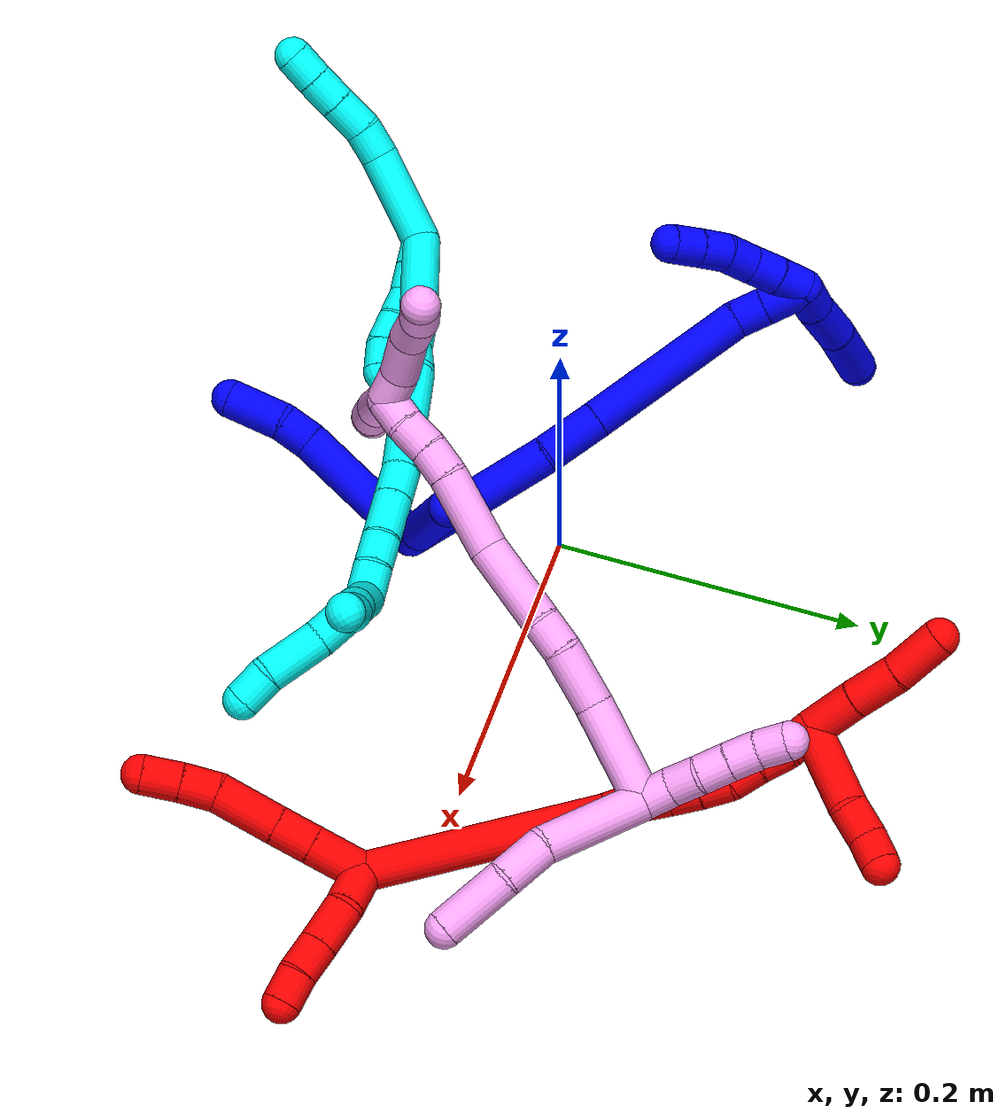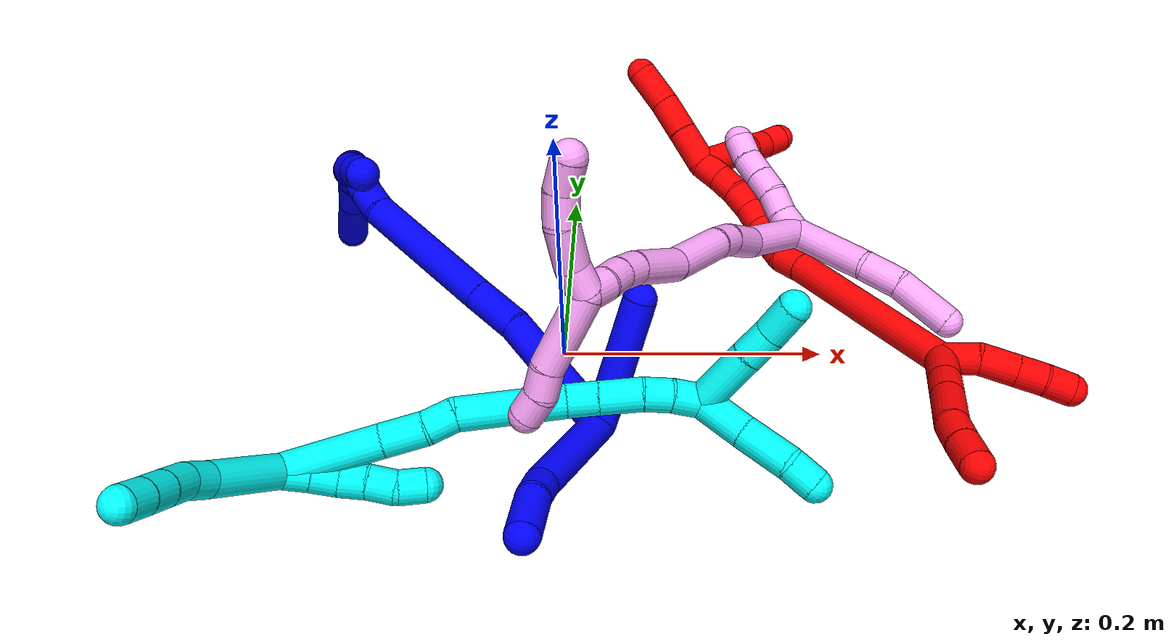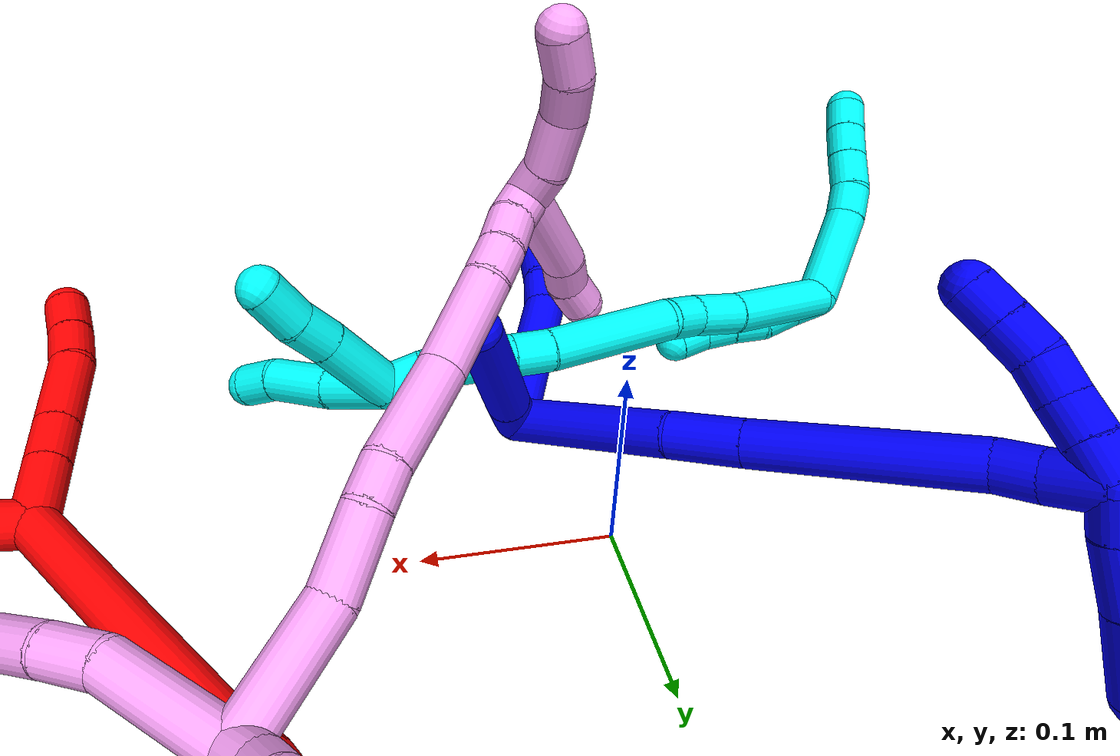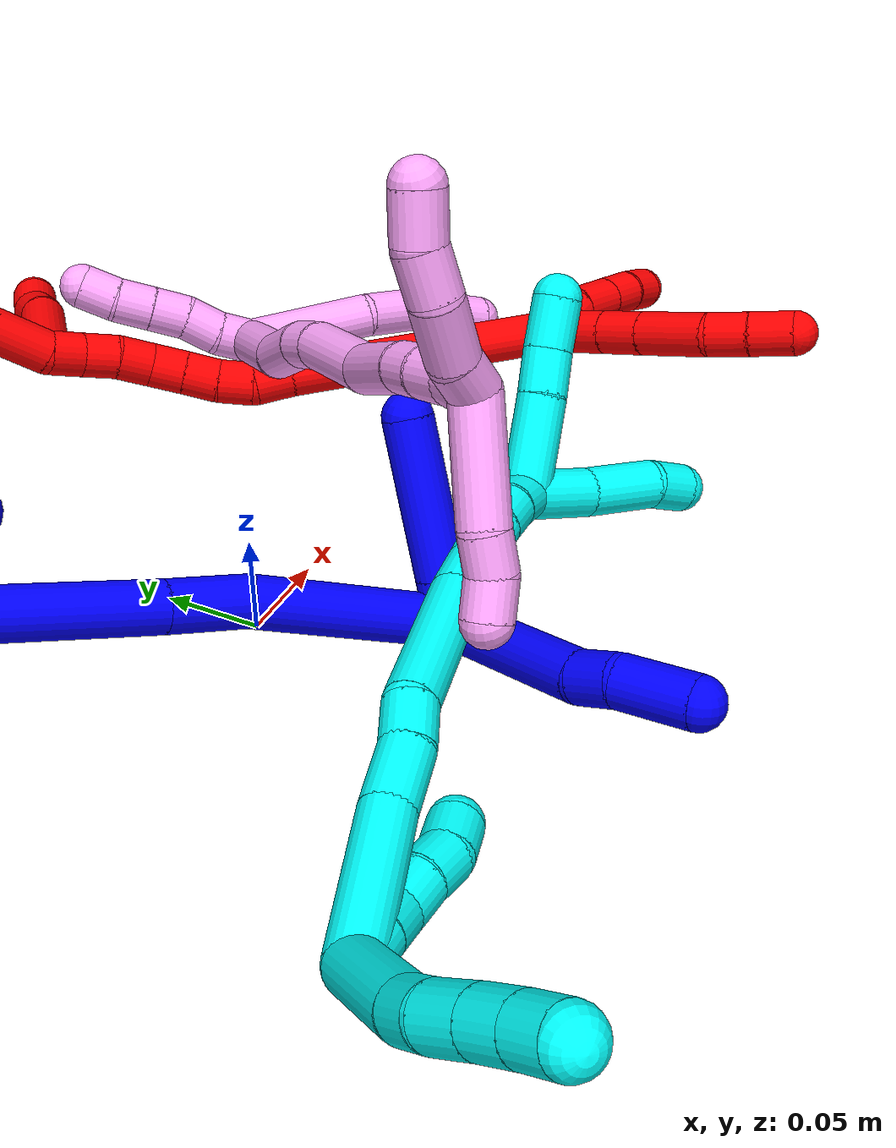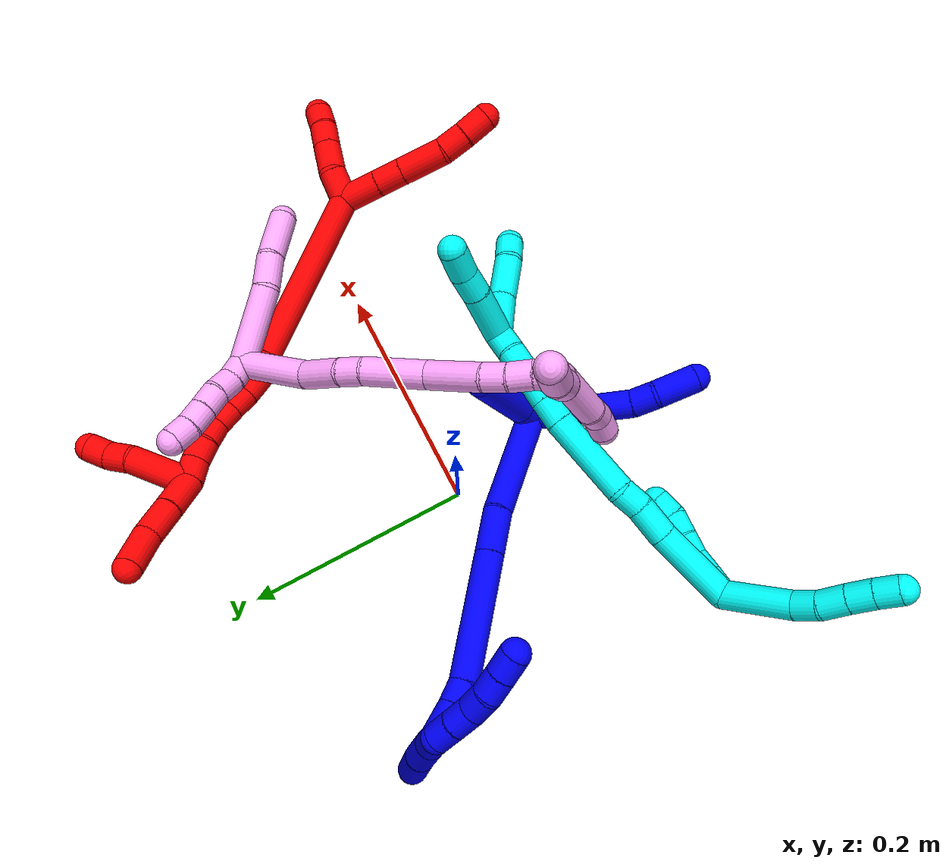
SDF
<sdf version="1.7">
 <world name="default">
  <plugin name="TubeGeneratorPlugin" filename="libtube_generator_plugin.so"/>
  <model name="photoneo_s_sensor">
   <static>1</static>
   <pose>0 0 2 1.57079 1.57079 3.14159</pose>
   <link name="link">
    <inertial><mass>0.1</mass></inertial>
    <sensor name="sensor" type="depth">
     <update_rate>30</update_rate>
     <camera>
      <horizontal_fov>1.22</horizontal_fov>
      <image><width>1920</width><height>1200</height><format>B8G8R8</format></image>
      <clip><near>0.1</near><far>4</far></clip>
      <depth_camera><output>points</output></depth_camera>
     </camera>
     <plugin name="camera_plugin" filename="libgazebo_ros_depth_camera.so">
      <baseline>0.2</baseline>
      <alwaysOn>1</alwaysOn>
      <updateRate>0.0</updateRate>
      <cameraName>camera_ir</cameraName>
      <imageTopicName>/camera/color/image_raw</imageTopicName>
      <cameraInfoTopicName>/camera/color/camera_info</cameraInfoTopicName>
      <depthImageTopicName>/camera/depth/image_raw</depthImageTopicName>
      <depthImageCameraInfoTopicName>/camera/depth/camera_info</depthImageCameraInfoTopicName>
      <pointCloudTopicName>/camera/depth/points</pointCloudTopicName>
      <frameName>fr_optical</frameName>
      <pointCloudCutoff>0.1</pointCloudCutoff>
      <pointCloudCutoffMax>2.0</pointCloudCutoffMax>
      <distortionK1>0</distortionK1>
      <distortionK2>0</distortionK2>
      <distortionK3>0</distortionK3>
      <distortionT1>0</distortionT1>
      <distortionT2>0</distortionT2>
      <CxPrime>0</CxPrime>
      <Cx>0</Cx>
      <Cy>0</Cy>
      <focalLength>0</focalLength>
      <hackBaseline>0</hackBaseline>
     </plugin>
    </sensor>
   </link>
  </model>
  <gravity>0 0 -9.8</gravity>
  <magnetic_field>6e-06 2.3e-05 -4.2e-05</magnetic_field>
  <atmosphere type="adiabatic"/>
  <physics name="default_physics" default="0" type="ode">
   <max_step_size>0.003</max_step_size>
   <real_time_factor>1</real_time_factor>
   <real_time_update_rate>1000</real_time_update_rate>
   <max_contacts>10000</max_contacts>
   <ode>
    <solver>
     <type>quick</type>
     <iters>100</iters>
     <sor>1.3</sor>
     <use_dynamic_moi_rescaling>0</use_dynamic_moi_rescaling>
    </solver>
    <constraints>
     <contact_max_correcting_vel>0</contact_max_correcting_vel>
     <contact_surface_layer>0.001</contact_surface_layer>
     <cfm>0</cfm>
     <erp>0.2</erp>
    </constraints>
   </ode>
  </physics>
  <scene><ambient>0.4 0.4 0.4 1</ambient><background>0.7 0.7 0.7 1</background><shadows>0</shadows></scene>
  <audio><device>default</device></audio>
  <spherical_coordinates>
   <surface_model>EARTH_WGS84</surface_model>
   <latitude_deg>0</latitude_deg>
   <longitude_deg>0</longitude_deg>
   <elevation>0</elevation>
   <heading_deg>0</heading_deg>
  </spherical_coordinates>
  <model name="bin">
   <static>1</static>
   <link name="bottom">
    <collision name="collision-bottom">
     <pose>0 0 -0.01 0 -0 0</pose>
     <geometry><box><size>0.8 0.6 0.02</size></box></geometry>
     <surface>
      <friction><ode><mu>100</mu><mu2>100</mu2></ode></friction>
      <contact><collide_bitmask>65535</collide_bitmask></contact>
     </surface>
    </collision>
   </link>
   <link name="west_wall">
    <collision name="collision-west_wall">
     <pose>-0.41 0 0.1 0 -0 0</pose>
     <geometry><box><size>0.02 0.6 0.2</size></box></geometry>
     <surface>
      <friction><ode><mu>100</mu><mu2>100</mu2></ode></friction>
      <contact><collide_bitmask>65535</collide_bitmask></contact>
     </surface>
    </collision>
   </link>
   <link name="east_wall">
    <collision name="collision-east_wall">
     <pose>0.41 0 0.1 0 -0 0</pose>
     <geometry><box><size>0.02 0.6 0.2</size></box></geometry>
     <surface>
      <friction><ode><mu>100</mu><mu2>100</mu2></ode></friction>
      <contact><collide_bitmask>65535</collide_bitmask></contact>
     </surface>
    </collision>
   </link>
   <link name="south_wall">
    <collision name="collision-south_wall">
     <pose>0 -0.31 0.1 0 -0 0</pose>
     <geometry><box><size>0.8 0.02 0.2</size></box></geometry>
     <surface>
      <friction><ode><mu>100</mu><mu2>100</mu2></ode></friction>
      <contact><collide_bitmask>65535</collide_bitmask></contact>
     </surface>
    </collision>
   </link>
   <link name="north_wall">
    <collision name="collision-north_wall">
     <pose>0 0.31 0.1 0 -0 0</pose>
     <geometry><box><size>0.8 0.02 0.2</size></box></geometry>
     <surface>
      <friction><ode><mu>100</mu><mu2>100</mu2></ode></friction>
      <contact><collide_bitmask>65535</collide_bitmask></contact>
     </surface>
    </collision>
   </link>
  </model>
  <model name="1">
   <static>0</static>
   <link name="1">
    <collision name="collision-cylinder-e_1_2_8">
     <pose>-0.034926 -0.028424 0.006551 1.34427 -0.874983 -0.712593</pose>
     <geometry><cylinder><radius>0.0125</radius><length>0.091009</length></cylinder></geometry>
     <surface>
      <friction><ode><mu>1.16</mu><mu2>1.16</mu2><slip1>0</slip1><slip2>0</slip2></ode></friction>
      <contact><ode><kp>1e+06</kp><kd>1</kd><max_vel>0</max_vel><min_depth>0.001</min_depth></ode></contact>
     </surface>
    </collision>
    <visual name="visual-cylinder-e_1_2_8">
     <pose>-0.034926 -0.028424 0.006551 1.34427 -0.874983 -0.712593</pose>
     <geometry><cylinder><radius>0.0125</radius><length>0.091009</length></cylinder></geometry>
     <material><ambient>0 0 1 1</ambient></material>
    </visual>
    <collision name="collision-cylinder-e_2_8_9">
     <pose>-0.076398 -0.064751 0.016442 1.17096 -0.651636 -0.440743</pose>
     <geometry><cylinder><radius>0.0125</radius><length>0.021583</length></cylinder></geometry>
     <surface>
      <friction><ode><mu>1.16</mu><mu2>1.16</mu2><slip1>0</slip1><slip2>0</slip2></ode></friction>
      <contact><ode><kp>1e+06</kp><kd>1</kd><max_vel>0</max_vel><min_depth>0.001</min_depth></ode></contact>
     </surface>
    </collision>
    <visual name="visual-cylinder-e_2_8_9">
     <pose>-0.076398 -0.064751 0.016442 1.17096 -0.651636 -0.440743</pose>
     <geometry><cylinder><radius>0.0125</radius><length>0.021583</length></cylinder></geometry>
     <material><ambient>0 0 1 1</ambient></material>
    </visual>
    <collision name="collision-cylinder-e_3_9_6">
     <pose>-0.092854 -0.088447 0.021264 1.47724 -0.558486 -0.510779</pose>
     <geometry><cylinder><radius>0.0125</radius><length>0.037407</length></cylinder></geometry>
     <surface>
      <friction><ode><mu>1.16</mu><mu2>1.16</mu2><slip1>0</slip1><slip2>0</slip2></ode></friction>
      <contact><ode><kp>1e+06</kp><kd>1</kd><max_vel>0</max_vel><min_depth>0.001</min_depth></ode></contact>
     </surface>
    </collision>
    <visual name="visual-cylinder-e_3_9_6">
     <pose>-0.092854 -0.088447 0.021264 1.47724 -0.558486 -0.510779</pose>
     <geometry><cylinder><radius>0.0125</radius><length>0.037407</length></cylinder></geometry>
     <material><ambient>0 0 1 1</ambient></material>
    </visual>
    <collision name="collision-cylinder-e_1_2_10">
     <pose>0.00287 0.00301 0.010367 -0.282618 0.259814 -0.037165</pose>
     <geometry><cylinder><radius>0.0125</radius><length>0.02234</length></cylinder></geometry>
     <surface>
      <friction><ode><mu>1.16</mu><mu2>1.16</mu2><slip1>0</slip1><slip2>0</slip2></ode></friction>
      <contact><ode><kp>1e+06</kp><kd>1</kd><max_vel>0</max_vel><min_depth>0.001</min_depth></ode></contact>
     </surface>
    </collision>
    <visual name="visual-cylinder-e_1_2_10">
     <pose>0.00287 0.00301 0.010367 -0.282618 0.259814 -0.037165</pose>
     <geometry><cylinder><radius>0.0125</radius><length>0.02234</length></cylinder></geometry>
     <material><ambient>0 0 1 1</ambient></material>
    </visual>
    <collision name="collision-cylinder-e_2_10_5">
     <pose>0.014662 0.016501 0.057042 -0.280994 0.231855 -0.032936</pose>
     <geometry><cylinder><radius>0.0125</radius><length>0.07766</length></cylinder></geometry>
     <surface>
      <friction><ode><mu>1.16</mu><mu2>1.16</mu2><slip1>0</slip1><slip2>0</slip2></ode></friction>
      <contact><ode><kp>1e+06</kp><kd>1</kd><max_vel>0</max_vel><min_depth>0.001</min_depth></ode></contact>
     </surface>
    </collision>
    <visual name="visual-cylinder-e_2_10_5">
     <pose>0.014662 0.016501 0.057042 -0.280994 0.231855 -0.032936</pose>
     <geometry><cylinder><radius>0.0125</radius><length>0.07766</length></cylinder></geometry>
     <material><ambient>0 0 1 1</ambient></material>
    </visual>
    <collision name="collision-cylinder-e_1_2_11">
     <pose>-0.017755 0.046335 0.010849 -1.34079 -0.357107 0.284267</pose>
     <geometry><cylinder><radius>0.0125</radius><length>0.101585</length></cylinder></geometry>
     <surface>
      <friction><ode><mu>1.16</mu><mu2>1.16</mu2><slip1>0</slip1><slip2>0</slip2></ode></friction>
      <contact><ode><kp>1e+06</kp><kd>1</kd><max_vel>0</max_vel><min_depth>0.001</min_depth></ode></contact>
     </surface>
    </collision>
    <visual name="visual-cylinder-e_1_2_11">
     <pose>-0.017755 0.046335 0.010849 -1.34079 -0.357107 0.284267</pose>
     <geometry><cylinder><radius>0.0125</radius><length>0.101585</length></cylinder></geometry>
     <material><ambient>0 0 1 1</ambient></material>
    </visual>
    <collision name="collision-cylinder-e_2_11_12">
     <pose>-0.044587 0.110083 0.023509 -1.4672 -0.478317 0.432699</pose>
     <geometry><cylinder><radius>0.0125</radius><length>0.03944</length></cylinder></geometry>
     <surface>
      <friction><ode><mu>1.16</mu><mu2>1.16</mu2><slip1>0</slip1><slip2>0</slip2></ode></friction>
      <contact><ode><kp>1e+06</kp><kd>1</kd><max_vel>0</max_vel><min_depth>0.001</min_depth></ode></contact>
     </surface>
    </collision>
    <visual name="visual-cylinder-e_2_11_12">
     <pose>-0.044587 0.110083 0.023509 -1.4672 -0.478317 0.432699</pose>
     <geometry><cylinder><radius>0.0125</radius><length>0.03944</length></cylinder></geometry>
     <material><ambient>0 0 1 1</ambient></material>
    </visual>
    <collision name="collision-cylinder-e_3_12_13">
     <pose>-0.079233 0.17599 0.032015 -1.43359 -0.481319 0.421368</pose>
     <geometry><cylinder><radius>0.0125</radius><length>0.110458</length></cylinder></geometry>
     <surface>
      <friction><ode><mu>1.16</mu><mu2>1.16</mu2><slip1>0</slip1><slip2>0</slip2></ode></friction>
      <contact><ode><kp>1e+06</kp><kd>1</kd><max_vel>0</max_vel><min_depth>0.001</min_depth></ode></contact>
     </surface>
    </collision>
    <visual name="visual-cylinder-e_3_12_13">
     <pose>-0.079233 0.17599 0.032015 -1.43359 -0.481319 0.421368</pose>
     <geometry><cylinder><radius>0.0125</radius><length>0.110458</length></cylinder></geometry>
     <material><ambient>0 0 1 1</ambient></material>
    </visual>
    <collision name="collision-cylinder-e_4_13_14">
     <pose>-0.10735 0.234422 0.040445 -1.39812 -0.247498 0.208379</pose>
     <geometry><cylinder><radius>0.0125</radius><length>0.02081</length></cylinder></geometry>
     <surface>
      <friction><ode><mu>1.16</mu><mu2>1.16</mu2><slip1>0</slip1><slip2>0</slip2></ode></friction>
      <contact><ode><kp>1e+06</kp><kd>1</kd><max_vel>0</max_vel><min_depth>0.001</min_depth></ode></contact>
     </surface>
    </collision>
    <visual name="visual-cylinder-e_4_13_14">
     <pose>-0.10735 0.234422 0.040445 -1.39812 -0.247498 0.208379</pose>
     <geometry><cylinder><radius>0.0125</radius><length>0.02081</length></cylinder></geometry>
     <material><ambient>0 0 1 1</ambient></material>
    </visual>
    <collision name="collision-cylinder-e_5_14_1">
     <pose>-0.112539 0.257314 0.046317 -1.26157 -0.191759 0.140245</pose>
     <geometry><cylinder><radius>0.0125</radius><length>0.027706</length></cylinder></geometry>
     <surface>
      <friction><ode><mu>1.16</mu><mu2>1.16</mu2><slip1>0</slip1><slip2>0</slip2></ode></friction>
      <contact><ode><kp>1e+06</kp><kd>1</kd><max_vel>0</max_vel><min_depth>0.001</min_depth></ode></contact>
     </surface>
    </collision>
    <visual name="visual-cylinder-e_5_14_1">
     <pose>-0.112539 0.257314 0.046317 -1.26157 -0.191759 0.140245</pose>
     <geometry><cylinder><radius>0.0125</radius><length>0.027706</length></cylinder></geometry>
     <material><ambient>0 0 1 1</ambient></material>
    </visual>
    <collision name="collision-cylinder-e_1_1_15">
     <pose>-0.118406 0.262259 0.055498 1.00889 -0.328531 -0.182519</pose>
     <geometry><cylinder><radius>0.0125</radius><length>0.02</length></cylinder></geometry>
     <surface>
      <friction><ode><mu>1.16</mu><mu2>1.16</mu2><slip1>0</slip1><slip2>0</slip2></ode></friction>
      <contact><ode><kp>1e+06</kp><kd>1</kd><max_vel>0</max_vel><min_depth>0.001</min_depth></ode></contact>
     </surface>
    </collision>
    <visual name="visual-cylinder-e_1_1_15">
     <pose>-0.118406 0.262259 0.055498 1.00889 -0.328531 -0.182519</pose>
     <geometry><cylinder><radius>0.0125</radius><length>0.02</length></cylinder></geometry>
     <material><ambient>0 0 1 1</ambient></material>
    </visual>
    <collision name="collision-cylinder-e_2_15_16">
     <pose>-0.124743 0.245971 0.065211 1.05716 -0.316267 -0.185723</pose>
     <geometry><cylinder><radius>0.0125</radius><length>0.02</length></cylinder></geometry>
     <surface>
      <friction><ode><mu>1.16</mu><mu2>1.16</mu2><slip1>0</slip1><slip2>0</slip2></ode></friction>
      <contact><ode><kp>1e+06</kp><kd>1</kd><max_vel>0</max_vel><min_depth>0.001</min_depth></ode></contact>
     </surface>
    </collision>
    <visual name="visual-cylinder-e_2_15_16">
     <pose>-0.124743 0.245971 0.065211 1.05716 -0.316267 -0.185723</pose>
     <geometry><cylinder><radius>0.0125</radius><length>0.02</length></cylinder></geometry>
     <material><ambient>0 0 1 1</ambient></material>
    </visual>
    <collision name="collision-cylinder-e_3_16_17">
     <pose>-0.130044 0.230098 0.076006 0.892189 -0.220884 -0.10597</pose>
     <geometry><cylinder><radius>0.0125</radius><length>0.02</length></cylinder></geometry>
     <surface>
      <friction><ode><mu>1.16</mu><mu2>1.16</mu2><slip1>0</slip1><slip2>0</slip2></ode></friction>
      <contact><ode><kp>1e+06</kp><kd>1</kd><max_vel>0</max_vel><min_depth>0.001</min_depth></ode></contact>
     </surface>
    </collision>
    <visual name="visual-cylinder-e_3_16_17">
     <pose>-0.130044 0.230098 0.076006 0.892189 -0.220884 -0.10597</pose>
     <geometry><cylinder><radius>0.0125</radius><length>0.02</length></cylinder></geometry>
     <material><ambient>0 0 1 1</ambient></material>
    </visual>
    <collision name="collision-cylinder-e_4_17_18">
     <pose>-0.132806 0.213843 0.087098 1.04993 -0.057195 -0.033132</pose>
     <geometry><cylinder><radius>0.0125</radius><length>0.02</length></cylinder></geometry>
     <surface>
      <friction><ode><mu>1.16</mu><mu2>1.16</mu2><slip1>0</slip1><slip2>0</slip2></ode></friction>
      <contact><ode><kp>1e+06</kp><kd>1</kd><max_vel>0</max_vel><min_depth>0.001</min_depth></ode></contact>
     </surface>
    </collision>
    <visual name="visual-cylinder-e_4_17_18">
     <pose>-0.132806 0.213843 0.087098 1.04993 -0.057195 -0.033132</pose>
     <geometry><cylinder><radius>0.0125</radius><length>0.02</length></cylinder></geometry>
     <material><ambient>0 0 1 1</ambient></material>
    </visual>
    <collision name="collision-cylinder-e_5_18_4">
     <pose>-0.133785 0.196428 0.096881 1.06807 -0.040754 -0.024102</pose>
     <geometry><cylinder><radius>0.0125</radius><length>0.02</length></cylinder></geometry>
     <surface>
      <friction><ode><mu>1.16</mu><mu2>1.16</mu2><slip1>0</slip1><slip2>0</slip2></ode></friction>
      <contact><ode><kp>1e+06</kp><kd>1</kd><max_vel>0</max_vel><min_depth>0.001</min_depth></ode></contact>
     </surface>
    </collision>
    <visual name="visual-cylinder-e_5_18_4">
     <pose>-0.133785 0.196428 0.096881 1.06807 -0.040754 -0.024102</pose>
     <geometry><cylinder><radius>0.0125</radius><length>0.02</length></cylinder></geometry>
     <material><ambient>0 0 1 1</ambient></material>
    </visual>
    <collision name="collision-cylinder-e_1_1_19">
     <pose>-0.112782 0.273251 0.040223 -2.85802 0.221205 -1.32236</pose>
     <geometry><cylinder><radius>0.0125</radius><length>0.021848</length></cylinder></geometry>
     <surface>
      <friction><ode><mu>1.16</mu><mu2>1.16</mu2><slip1>0</slip1><slip2>0</slip2></ode></friction>
      <contact><ode><kp>1e+06</kp><kd>1</kd><max_vel>0</max_vel><min_depth>0.001</min_depth></ode></contact>
     </surface>
    </collision>
    <visual name="visual-cylinder-e_1_1_19">
     <pose>-0.112782 0.273251 0.040223 -2.85802 0.221205 -1.32236</pose>
     <geometry><cylinder><radius>0.0125</radius><length>0.021848</length></cylinder></geometry>
     <material><ambient>0 0 1 1</ambient></material>
    </visual>
    <collision name="collision-cylinder-e_2_19_20">
     <pose>-0.107268 0.282765 0.014781 -2.73593 0.186134 -0.852085</pose>
     <geometry><cylinder><radius>0.0125</radius><length>0.033688</length></cylinder></geometry>
     <surface>
      <friction><ode><mu>1.16</mu><mu2>1.16</mu2><slip1>0</slip1><slip2>0</slip2></ode></friction>
      <contact><ode><kp>1e+06</kp><kd>1</kd><max_vel>0</max_vel><min_depth>0.001</min_depth></ode></contact>
     </surface>
    </collision>
    <visual name="visual-cylinder-e_2_19_20">
     <pose>-0.107268 0.282765 0.014781 -2.73593 0.186134 -0.852085</pose>
     <geometry><cylinder><radius>0.0125</radius><length>0.033688</length></cylinder></geometry>
     <material><ambient>0 0 1 1</ambient></material>
    </visual>
    <collision name="collision-cylinder-e_3_20_3">
     <pose>-0.100884 0.295835 -0.021425 -2.83972 0.14751 -0.904463</pose>
     <geometry><cylinder><radius>0.0125</radius><length>0.044464</length></cylinder></geometry>
     <surface>
      <friction><ode><mu>1.16</mu><mu2>1.16</mu2><slip1>0</slip1><slip2>0</slip2></ode></friction>
      <contact><ode><kp>1e+06</kp><kd>1</kd><max_vel>0</max_vel><min_depth>0.001</min_depth></ode></contact>
     </surface>
    </collision>
    <visual name="visual-cylinder-e_3_20_3">
     <pose>-0.100884 0.295835 -0.021425 -2.83972 0.14751 -0.904463</pose>
     <geometry><cylinder><radius>0.0125</radius><length>0.044464</length></cylinder></geometry>
     <material><ambient>0 0 1 1</ambient></material>
    </visual>
    <collision name="collision-sphere-3">
     <pose>-0.097616 0.302373 -0.042421 0 -0 0</pose>
     <geometry><sphere><radius>0.0125</radius></sphere></geometry>
     <surface>
      <friction><ode><mu>1.16</mu><mu2>1.16</mu2><slip1>0</slip1><slip2>0</slip2></ode></friction>
      <contact><ode><kp>1e+06</kp><kd>1</kd><max_vel>0</max_vel><min_depth>0.001</min_depth></ode></contact>
     </surface>
    </collision>
    <visual name="visual-sphere-3">
     <pose>-0.097616 0.302373 -0.042421 0 -0 0</pose>
     <geometry><sphere><radius>0.0125</radius></sphere></geometry>
     <material><ambient>0 0 1 1</ambient></material>
    </visual>
    <collision name="collision-sphere-20">
     <pose>-0.104151 0.289297 -0.000429 0 -0 0</pose>
     <geometry><sphere><radius>0.0125</radius></sphere></geometry>
     <surface>
      <friction><ode><mu>1.16</mu><mu2>1.16</mu2><slip1>0</slip1><slip2>0</slip2></ode></friction>
      <contact><ode><kp>1e+06</kp><kd>1</kd><max_vel>0</max_vel><min_depth>0.001</min_depth></ode></contact>
     </surface>
    </collision>
    <visual name="visual-sphere-20">
     <pose>-0.104151 0.289297 -0.000429 0 -0 0</pose>
     <geometry><sphere><radius>0.0125</radius></sphere></geometry>
     <material><ambient>0 0 1 1</ambient></material>
    </visual>
    <collision name="collision-sphere-19">
     <pose>-0.110386 0.276233 0.029991 0 -0 0</pose>
     <geometry><sphere><radius>0.0125</radius></sphere></geometry>
     <surface>
      <friction><ode><mu>1.16</mu><mu2>1.16</mu2><slip1>0</slip1><slip2>0</slip2></ode></friction>
      <contact><ode><kp>1e+06</kp><kd>1</kd><max_vel>0</max_vel><min_depth>0.001</min_depth></ode></contact>
     </surface>
    </collision>
    <visual name="visual-sphere-19">
     <pose>-0.110386 0.276233 0.029991 0 -0 0</pose>
     <geometry><sphere><radius>0.0125</radius></sphere></geometry>
     <material><ambient>0 0 1 1</ambient></material>
    </visual>
    <collision name="collision-sphere-5">
     <pose>0.023584 0.026981 0.093351 0 -0 0</pose>
     <geometry><sphere><radius>0.0125</radius></sphere></geometry>
     <surface>
      <friction><ode><mu>1.16</mu><mu2>1.16</mu2><slip1>0</slip1><slip2>0</slip2></ode></friction>
      <contact><ode><kp>1e+06</kp><kd>1</kd><max_vel>0</max_vel><min_depth>0.001</min_depth></ode></contact>
     </surface>
    </collision>
    <visual name="visual-sphere-5">
     <pose>0.023584 0.026981 0.093351 0 -0 0</pose>
     <geometry><sphere><radius>0.0125</radius></sphere></geometry>
     <material><ambient>0 0 1 1</ambient></material>
    </visual>
    <collision name="collision-sphere-10">
     <pose>0.005739 0.006021 0.020733 0 -0 0</pose>
     <geometry><sphere><radius>0.0125</radius></sphere></geometry>
     <surface>
      <friction><ode><mu>1.16</mu><mu2>1.16</mu2><slip1>0</slip1><slip2>0</slip2></ode></friction>
      <contact><ode><kp>1e+06</kp><kd>1</kd><max_vel>0</max_vel><min_depth>0.001</min_depth></ode></contact>
     </surface>
    </collision>
    <visual name="visual-sphere-10">
     <pose>0.005739 0.006021 0.020733 0 -0 0</pose>
     <geometry><sphere><radius>0.0125</radius></sphere></geometry>
     <material><ambient>0 0 1 1</ambient></material>
    </visual>
    <collision name="collision-sphere-6">
     <pose>-0.102765 -0.10424 0.022746 0 -0 0</pose>
     <geometry><sphere><radius>0.0125</radius></sphere></geometry>
     <surface>
      <friction><ode><mu>1.16</mu><mu2>1.16</mu2><slip1>0</slip1><slip2>0</slip2></ode></friction>
      <contact><ode><kp>1e+06</kp><kd>1</kd><max_vel>0</max_vel><min_depth>0.001</min_depth></ode></contact>
     </surface>
    </collision>
    <visual name="visual-sphere-6">
     <pose>-0.102765 -0.10424 0.022746 0 -0 0</pose>
     <geometry><sphere><radius>0.0125</radius></sphere></geometry>
     <material><ambient>0 0 1 1</ambient></material>
    </visual>
    <collision name="collision-sphere-9">
     <pose>-0.082943 -0.072655 0.019783 0 -0 0</pose>
     <geometry><sphere><radius>0.0125</radius></sphere></geometry>
     <surface>
      <friction><ode><mu>1.16</mu><mu2>1.16</mu2><slip1>0</slip1><slip2>0</slip2></ode></friction>
      <contact><ode><kp>1e+06</kp><kd>1</kd><max_vel>0</max_vel><min_depth>0.001</min_depth></ode></contact>
     </surface>
    </collision>
    <visual name="visual-sphere-9">
     <pose>-0.082943 -0.072655 0.019783 0 -0 0</pose>
     <geometry><sphere><radius>0.0125</radius></sphere></geometry>
     <material><ambient>0 0 1 1</ambient></material>
    </visual>
    <collision name="collision-sphere-2">
     <geometry><sphere><radius>0.0125</radius></sphere></geometry>
     <surface>
      <friction><ode><mu>1.16</mu><mu2>1.16</mu2><slip1>0</slip1><slip2>0</slip2></ode></friction>
      <contact><ode><kp>1e+06</kp><kd>1</kd><max_vel>0</max_vel><min_depth>0.001</min_depth></ode></contact>
     </surface>
    </collision>
    <visual name="visual-sphere-2">
     <geometry><sphere><radius>0.0125</radius></sphere></geometry>
     <material><ambient>0 0 1 1</ambient></material>
    </visual>
    <collision name="collision-sphere-8">
     <pose>-0.069853 -0.056848 0.013102 0 -0 0</pose>
     <geometry><sphere><radius>0.0125</radius></sphere></geometry>
     <surface>
      <friction><ode><mu>1.16</mu><mu2>1.16</mu2><slip1>0</slip1><slip2>0</slip2></ode></friction>
      <contact><ode><kp>1e+06</kp><kd>1</kd><max_vel>0</max_vel><min_depth>0.001</min_depth></ode></contact>
     </surface>
    </collision>
    <visual name="visual-sphere-8">
     <pose>-0.069853 -0.056848 0.013102 0 -0 0</pose>
     <geometry><sphere><radius>0.0125</radius></sphere></geometry>
     <material><ambient>0 0 1 1</ambient></material>
    </visual>
    <collision name="collision-sphere-11">
     <pose>-0.035511 0.09267 0.021699 0 -0 0</pose>
     <geometry><sphere><radius>0.0125</radius></sphere></geometry>
     <surface>
      <friction><ode><mu>1.16</mu><mu2>1.16</mu2><slip1>0</slip1><slip2>0</slip2></ode></friction>
      <contact><ode><kp>1e+06</kp><kd>1</kd><max_vel>0</max_vel><min_depth>0.001</min_depth></ode></contact>
     </surface>
    </collision>
    <visual name="visual-sphere-11">
     <pose>-0.035511 0.09267 0.021699 0 -0 0</pose>
     <geometry><sphere><radius>0.0125</radius></sphere></geometry>
     <material><ambient>0 0 1 1</ambient></material>
    </visual>
    <collision name="collision-sphere-12">
     <pose>-0.053664 0.127496 0.02532 0 -0 0</pose>
     <geometry><sphere><radius>0.0125</radius></sphere></geometry>
     <surface>
      <friction><ode><mu>1.16</mu><mu2>1.16</mu2><slip1>0</slip1><slip2>0</slip2></ode></friction>
      <contact><ode><kp>1e+06</kp><kd>1</kd><max_vel>0</max_vel><min_depth>0.001</min_depth></ode></contact>
     </surface>
    </collision>
    <visual name="visual-sphere-12">
     <pose>-0.053664 0.127496 0.02532 0 -0 0</pose>
     <geometry><sphere><radius>0.0125</radius></sphere></geometry>
     <material><ambient>0 0 1 1</ambient></material>
    </visual>
    <collision name="collision-sphere-13">
     <pose>-0.104801 0.224484 0.038711 0 -0 0</pose>
     <geometry><sphere><radius>0.0125</radius></sphere></geometry>
     <surface>
      <friction><ode><mu>1.16</mu><mu2>1.16</mu2><slip1>0</slip1><slip2>0</slip2></ode></friction>
      <contact><ode><kp>1e+06</kp><kd>1</kd><max_vel>0</max_vel><min_depth>0.001</min_depth></ode></contact>
     </surface>
    </collision>
    <visual name="visual-sphere-13">
     <pose>-0.104801 0.224484 0.038711 0 -0 0</pose>
     <geometry><sphere><radius>0.0125</radius></sphere></geometry>
     <material><ambient>0 0 1 1</ambient></material>
    </visual>
    <collision name="collision-sphere-14">
     <pose>-0.109899 0.24436 0.042178 0 -0 0</pose>
     <geometry><sphere><radius>0.0125</radius></sphere></geometry>
     <surface>
      <friction><ode><mu>1.16</mu><mu2>1.16</mu2><slip1>0</slip1><slip2>0</slip2></ode></friction>
      <contact><ode><kp>1e+06</kp><kd>1</kd><max_vel>0</max_vel><min_depth>0.001</min_depth></ode></contact>
     </surface>
    </collision>
    <visual name="visual-sphere-14">
     <pose>-0.109899 0.24436 0.042178 0 -0 0</pose>
     <geometry><sphere><radius>0.0125</radius></sphere></geometry>
     <material><ambient>0 0 1 1</ambient></material>
    </visual>
    <collision name="collision-sphere-1">
     <pose>-0.115179 0.270269 0.050455 0 -0 0</pose>
     <geometry><sphere><radius>0.0125</radius></sphere></geometry>
     <surface>
      <friction><ode><mu>1.16</mu><mu2>1.16</mu2><slip1>0</slip1><slip2>0</slip2></ode></friction>
      <contact><ode><kp>1e+06</kp><kd>1</kd><max_vel>0</max_vel><min_depth>0.001</min_depth></ode></contact>
     </surface>
    </collision>
    <visual name="visual-sphere-1">
     <pose>-0.115179 0.270269 0.050455 0 -0 0</pose>
     <geometry><sphere><radius>0.0125</radius></sphere></geometry>
     <material><ambient>0 0 1 1</ambient></material>
    </visual>
    <collision name="collision-sphere-18">
     <pose>-0.133378 0.205184 0.092066 0 -0 0</pose>
     <geometry><sphere><radius>0.0125</radius></sphere></geometry>
     <surface>
      <friction><ode><mu>1.16</mu><mu2>1.16</mu2><slip1>0</slip1><slip2>0</slip2></ode></friction>
      <contact><ode><kp>1e+06</kp><kd>1</kd><max_vel>0</max_vel><min_depth>0.001</min_depth></ode></contact>
     </surface>
    </collision>
    <visual name="visual-sphere-18">
     <pose>-0.133378 0.205184 0.092066 0 -0 0</pose>
     <geometry><sphere><radius>0.0125</radius></sphere></geometry>
     <material><ambient>0 0 1 1</ambient></material>
    </visual>
    <collision name="collision-sphere-15">
     <pose>-0.121632 0.254249 0.060541 0 -0 0</pose>
     <geometry><sphere><radius>0.0125</radius></sphere></geometry>
     <surface>
      <friction><ode><mu>1.16</mu><mu2>1.16</mu2><slip1>0</slip1><slip2>0</slip2></ode></friction>
      <contact><ode><kp>1e+06</kp><kd>1</kd><max_vel>0</max_vel><min_depth>0.001</min_depth></ode></contact>
     </surface>
    </collision>
    <visual name="visual-sphere-15">
     <pose>-0.121632 0.254249 0.060541 0 -0 0</pose>
     <geometry><sphere><radius>0.0125</radius></sphere></geometry>
     <material><ambient>0 0 1 1</ambient></material>
    </visual>
    <collision name="collision-sphere-16">
     <pose>-0.127853 0.237694 0.069881 0 -0 0</pose>
     <geometry><sphere><radius>0.0125</radius></sphere></geometry>
     <surface>
      <friction><ode><mu>1.16</mu><mu2>1.16</mu2><slip1>0</slip1><slip2>0</slip2></ode></friction>
      <contact><ode><kp>1e+06</kp><kd>1</kd><max_vel>0</max_vel><min_depth>0.001</min_depth></ode></contact>
     </surface>
    </collision>
    <visual name="visual-sphere-16">
     <pose>-0.127853 0.237694 0.069881 0 -0 0</pose>
     <geometry><sphere><radius>0.0125</radius></sphere></geometry>
     <material><ambient>0 0 1 1</ambient></material>
    </visual>
    <collision name="collision-sphere-17">
     <pose>-0.132235 0.222503 0.08213 0 -0 0</pose>
     <geometry><sphere><radius>0.0125</radius></sphere></geometry>
     <surface>
      <friction><ode><mu>1.16</mu><mu2>1.16</mu2><slip1>0</slip1><slip2>0</slip2></ode></friction>
      <contact><ode><kp>1e+06</kp><kd>1</kd><max_vel>0</max_vel><min_depth>0.001</min_depth></ode></contact>
     </surface>
    </collision>
    <visual name="visual-sphere-17">
     <pose>-0.132235 0.222503 0.08213 0 -0 0</pose>
     <geometry><sphere><radius>0.0125</radius></sphere></geometry>
     <material><ambient>0 0 1 1</ambient></material>
    </visual>
    <collision name="collision-sphere-4">
     <pose>-0.134193 0.187673 0.101695 0 -0 0</pose>
     <geometry><sphere><radius>0.0125</radius></sphere></geometry>
     <surface>
      <friction><ode><mu>1.16</mu><mu2>1.16</mu2><slip1>0</slip1><slip2>0</slip2></ode></friction>
      <contact><ode><kp>1e+06</kp><kd>1</kd><max_vel>0</max_vel><min_depth>0.001</min_depth></ode></contact>
     </surface>
    </collision>
    <visual name="visual-sphere-4">
     <pose>-0.134193 0.187673 0.101695 0 -0 0</pose>
     <geometry><sphere><radius>0.0125</radius></sphere></geometry>
     <material><ambient>0 0 1 1</ambient></material>
    </visual>
    <inertial>
     <pose>-0.064165 0.114898 0.029516 0 -0 0</pose>
     <mass>0.75</mass>
     <inertia>
      <ixx>0.000292</ixx>
      <ixy>0</ixy>
      <ixz>0</ixz>
      <iyy>0.000189</iyy>
      <iyz>0</iyz>
      <izz>-1.5e-05</izz>
     </inertia>
    </inertial>
   </link>
   <pose>0.030911 -0.08988 0.01149 0.072837 0.20514 0.441193</pose>
  </model>
  <model name="2">
   <static>0</static>
   <link name="2">
    <collision name="collision-cylinder-e_1_2_8">
     <pose>0.006034 -0.016121 -0.002976 1.75336 0.352666 0.421816</pose>
     <geometry><cylinder><radius>0.0125</radius><length>0.034937</length></cylinder></geometry>
     <surface>
      <friction><ode><mu>1.16</mu><mu2>1.16</mu2><slip1>0</slip1><slip2>0</slip2></ode></friction>
      <contact><ode><kp>1e+06</kp><kd>1</kd><max_vel>0</max_vel><min_depth>0.001</min_depth></ode></contact>
     </surface>
    </collision>
    <visual name="visual-cylinder-e_1_2_8">
     <pose>0.006034 -0.016121 -0.002976 1.75336 0.352666 0.421816</pose>
     <geometry><cylinder><radius>0.0125</radius><length>0.034937</length></cylinder></geometry>
     <material><ambient>1 0 0 1</ambient></material>
    </visual>
    <collision name="collision-cylinder-e_2_8_9">
     <pose>0.016473 -0.043834 -0.008078 1.75215 0.357719 0.427292</pose>
     <geometry><cylinder><radius>0.0125</radius><length>0.025163</length></cylinder></geometry>
     <surface>
      <friction><ode><mu>1.16</mu><mu2>1.16</mu2><slip1>0</slip1><slip2>0</slip2></ode></friction>
      <contact><ode><kp>1e+06</kp><kd>1</kd><max_vel>0</max_vel><min_depth>0.001</min_depth></ode></contact>
     </surface>
    </collision>
    <visual name="visual-cylinder-e_2_8_9">
     <pose>0.016473 -0.043834 -0.008078 1.75215 0.357719 0.427292</pose>
     <geometry><cylinder><radius>0.0125</radius><length>0.025163</length></cylinder></geometry>
     <material><ambient>1 0 0 1</ambient></material>
    </visual>
    <collision name="collision-cylinder-e_3_9_10">
     <pose>0.027869 -0.074534 -0.01392 1.76288 0.344813 0.416405</pose>
     <geometry><cylinder><radius>0.0125</radius><length>0.041366</length></cylinder></geometry>
     <surface>
      <friction><ode><mu>1.16</mu><mu2>1.16</mu2><slip1>0</slip1><slip2>0</slip2></ode></friction>
      <contact><ode><kp>1e+06</kp><kd>1</kd><max_vel>0</max_vel><min_depth>0.001</min_depth></ode></contact>
     </surface>
    </collision>
    <visual name="visual-cylinder-e_3_9_10">
     <pose>0.027869 -0.074534 -0.01392 1.76288 0.344813 0.416405</pose>
     <geometry><cylinder><radius>0.0125</radius><length>0.041366</length></cylinder></geometry>
     <material><ambient>1 0 0 1</ambient></material>
    </visual>
    <collision name="collision-cylinder-e_4_10_11">
     <pose>0.03934 -0.104548 -0.016894 1.50285 0.38886 0.363877</pose>
     <geometry><cylinder><radius>0.0125</radius><length>0.023628</length></cylinder></geometry>
     <surface>
      <friction><ode><mu>1.16</mu><mu2>1.16</mu2><slip1>0</slip1><slip2>0</slip2></ode></friction>
      <contact><ode><kp>1e+06</kp><kd>1</kd><max_vel>0</max_vel><min_depth>0.001</min_depth></ode></contact>
     </surface>
    </collision>
    <visual name="visual-cylinder-e_4_10_11">
     <pose>0.03934 -0.104548 -0.016894 1.50285 0.38886 0.363877</pose>
     <geometry><cylinder><radius>0.0125</radius><length>0.023628</length></cylinder></geometry>
     <material><ambient>1 0 0 1</ambient></material>
    </visual>
    <collision name="collision-cylinder-e_5_11_6">
     <pose>0.048658 -0.126818 -0.014557 1.43137 0.399106 0.348129</pose>
     <geometry><cylinder><radius>0.0125</radius><length>0.024905</length></cylinder></geometry>
     <surface>
      <friction><ode><mu>1.16</mu><mu2>1.16</mu2><slip1>0</slip1><slip2>0</slip2></ode></friction>
      <contact><ode><kp>1e+06</kp><kd>1</kd><max_vel>0</max_vel><min_depth>0.001</min_depth></ode></contact>
     </surface>
    </collision>
    <visual name="visual-cylinder-e_5_11_6">
     <pose>0.048658 -0.126818 -0.014557 1.43137 0.399106 0.348129</pose>
     <geometry><cylinder><radius>0.0125</radius><length>0.024905</length></cylinder></geometry>
     <material><ambient>1 0 0 1</ambient></material>
    </visual>
    <collision name="collision-cylinder-e_1_2_12">
     <pose>-0.002024 -0.002992 0.013701 0.214989 -0.143334 -0.015493</pose>
     <geometry><cylinder><radius>0.0125</radius><length>0.028339</length></cylinder></geometry>
     <surface>
      <friction><ode><mu>1.16</mu><mu2>1.16</mu2><slip1>0</slip1><slip2>0</slip2></ode></friction>
      <contact><ode><kp>1e+06</kp><kd>1</kd><max_vel>0</max_vel><min_depth>0.001</min_depth></ode></contact>
     </surface>
    </collision>
    <visual name="visual-cylinder-e_1_2_12">
     <pose>-0.002024 -0.002992 0.013701 0.214989 -0.143334 -0.015493</pose>
     <geometry><cylinder><radius>0.0125</radius><length>0.028339</length></cylinder></geometry>
     <material><ambient>1 0 0 1</ambient></material>
    </visual>
    <collision name="collision-cylinder-e_2_12_13">
     <pose>-0.001557 -0.009107 0.041263 0.221607 0.173596 0.019362</pose>
     <geometry><cylinder><radius>0.0125</radius><length>0.028849</length></cylinder></geometry>
     <surface>
      <friction><ode><mu>1.16</mu><mu2>1.16</mu2><slip1>0</slip1><slip2>0</slip2></ode></friction>
      <contact><ode><kp>1e+06</kp><kd>1</kd><max_vel>0</max_vel><min_depth>0.001</min_depth></ode></contact>
     </surface>
    </collision>
    <visual name="visual-cylinder-e_2_12_13">
     <pose>-0.001557 -0.009107 0.041263 0.221607 0.173596 0.019362</pose>
     <geometry><cylinder><radius>0.0125</radius><length>0.028849</length></cylinder></geometry>
     <material><ambient>1 0 0 1</ambient></material>
    </visual>
    <collision name="collision-cylinder-e_3_13_14">
     <pose>0.002838 -0.014872 0.065642 0.246103 0.173687 0.021534</pose>
     <geometry><cylinder><radius>0.0125</radius><length>0.022023</length></cylinder></geometry>
     <surface>
      <friction><ode><mu>1.16</mu><mu2>1.16</mu2><slip1>0</slip1><slip2>0</slip2></ode></friction>
      <contact><ode><kp>1e+06</kp><kd>1</kd><max_vel>0</max_vel><min_depth>0.001</min_depth></ode></contact>
     </surface>
    </collision>
    <visual name="visual-cylinder-e_3_13_14">
     <pose>0.002838 -0.014872 0.065642 0.246103 0.173687 0.021534</pose>
     <geometry><cylinder><radius>0.0125</radius><length>0.022023</length></cylinder></geometry>
     <material><ambient>1 0 0 1</ambient></material>
    </visual>
    <collision name="collision-cylinder-e_4_14_5">
     <pose>0.00714 -0.018378 0.086238 0.085555 0.232959 0.010017</pose>
     <geometry><cylinder><radius>0.0125</radius><length>0.020789</length></cylinder></geometry>
     <surface>
      <friction><ode><mu>1.16</mu><mu2>1.16</mu2><slip1>0</slip1><slip2>0</slip2></ode></friction>
      <contact><ode><kp>1e+06</kp><kd>1</kd><max_vel>0</max_vel><min_depth>0.001</min_depth></ode></contact>
     </surface>
    </collision>
    <visual name="visual-cylinder-e_4_14_5">
     <pose>0.00714 -0.018378 0.086238 0.085555 0.232959 0.010017</pose>
     <geometry><cylinder><radius>0.0125</radius><length>0.020789</length></cylinder></geometry>
     <material><ambient>1 0 0 1</ambient></material>
    </visual>
    <collision name="collision-cylinder-e_1_2_15">
     <pose>-0.024726 0.060696 -0.043906 -2.19703 -0.318812 0.60981</pose>
     <geometry><cylinder><radius>0.0125</radius><length>0.157774</length></cylinder></geometry>
     <surface>
      <friction><ode><mu>1.16</mu><mu2>1.16</mu2><slip1>0</slip1><slip2>0</slip2></ode></friction>
      <contact><ode><kp>1e+06</kp><kd>1</kd><max_vel>0</max_vel><min_depth>0.001</min_depth></ode></contact>
     </surface>
    </collision>
    <visual name="visual-cylinder-e_1_2_15">
     <pose>-0.024726 0.060696 -0.043906 -2.19703 -0.318812 0.60981</pose>
     <geometry><cylinder><radius>0.0125</radius><length>0.157774</length></cylinder></geometry>
     <material><ambient>1 0 0 1</ambient></material>
    </visual>
    <collision name="collision-cylinder-e_2_15_16">
     <pose>-0.052208 0.129433 -0.09483 -2.2885 -0.252668 0.545057</pose>
     <geometry><cylinder><radius>0.0125</radius><length>0.022045</length></cylinder></geometry>
     <surface>
      <friction><ode><mu>1.16</mu><mu2>1.16</mu2><slip1>0</slip1><slip2>0</slip2></ode></friction>
      <contact><ode><kp>1e+06</kp><kd>1</kd><max_vel>0</max_vel><min_depth>0.001</min_depth></ode></contact>
     </surface>
    </collision>
    <visual name="visual-cylinder-e_2_15_16">
     <pose>-0.052208 0.129433 -0.09483 -2.2885 -0.252668 0.545057</pose>
     <geometry><cylinder><radius>0.0125</radius><length>0.022045</length></cylinder></geometry>
     <material><ambient>1 0 0 1</ambient></material>
    </visual>
    <collision name="collision-cylinder-e_3_16_17">
     <pose>-0.060351 0.144732 -0.106312 -2.12199 -0.563766 0.955832</pose>
     <geometry><cylinder><radius>0.0125</radius><length>0.020164</length></cylinder></geometry>
     <surface>
      <friction><ode><mu>1.16</mu><mu2>1.16</mu2><slip1>0</slip1><slip2>0</slip2></ode></friction>
      <contact><ode><kp>1e+06</kp><kd>1</kd><max_vel>0</max_vel><min_depth>0.001</min_depth></ode></contact>
     </surface>
    </collision>
    <visual name="visual-cylinder-e_3_16_17">
     <pose>-0.060351 0.144732 -0.106312 -2.12199 -0.563766 0.955832</pose>
     <geometry><cylinder><radius>0.0125</radius><length>0.020164</length></cylinder></geometry>
     <material><ambient>1 0 0 1</ambient></material>
    </visual>
    <collision name="collision-cylinder-e_4_17_18">
     <pose>-0.07238 0.158332 -0.114753 -2.13121 -0.725702 1.20317</pose>
     <geometry><cylinder><radius>0.0125</radius><length>0.020014</length></cylinder></geometry>
     <surface>
      <friction><ode><mu>1.16</mu><mu2>1.16</mu2><slip1>0</slip1><slip2>0</slip2></ode></friction>
      <contact><ode><kp>1e+06</kp><kd>1</kd><max_vel>0</max_vel><min_depth>0.001</min_depth></ode></contact>
     </surface>
    </collision>
    <visual name="visual-cylinder-e_4_17_18">
     <pose>-0.07238 0.158332 -0.114753 -2.13121 -0.725702 1.20317</pose>
     <geometry><cylinder><radius>0.0125</radius><length>0.020014</length></cylinder></geometry>
     <material><ambient>1 0 0 1</ambient></material>
    </visual>
    <collision name="collision-cylinder-e_5_18_19">
     <pose>-0.085602 0.170714 -0.123228 -2.21052 -0.718204 1.28344</pose>
     <geometry><cylinder><radius>0.0125</radius><length>0.020001</length></cylinder></geometry>
     <surface>
      <friction><ode><mu>1.16</mu><mu2>1.16</mu2><slip1>0</slip1><slip2>0</slip2></ode></friction>
      <contact><ode><kp>1e+06</kp><kd>1</kd><max_vel>0</max_vel><min_depth>0.001</min_depth></ode></contact>
     </surface>
    </collision>
    <visual name="visual-cylinder-e_5_18_19">
     <pose>-0.085602 0.170714 -0.123228 -2.21052 -0.718204 1.28344</pose>
     <geometry><cylinder><radius>0.0125</radius><length>0.020001</length></cylinder></geometry>
     <material><ambient>1 0 0 1</ambient></material>
    </visual>
    <collision name="collision-cylinder-e_6_19_20">
     <pose>-0.0986 0.180905 -0.134173 -2.56994 -0.696758 1.78101</pose>
     <geometry><cylinder><radius>0.0125</radius><length>0.02</length></cylinder></geometry>
     <surface>
      <friction><ode><mu>1.16</mu><mu2>1.16</mu2><slip1>0</slip1><slip2>0</slip2></ode></friction>
      <contact><ode><kp>1e+06</kp><kd>1</kd><max_vel>0</max_vel><min_depth>0.001</min_depth></ode></contact>
     </surface>
    </collision>
    <visual name="visual-cylinder-e_6_19_20">
     <pose>-0.0986 0.180905 -0.134173 -2.56994 -0.696758 1.78101</pose>
     <geometry><cylinder><radius>0.0125</radius><length>0.02</length></cylinder></geometry>
     <material><ambient>1 0 0 1</ambient></material>
    </visual>
    <collision name="collision-cylinder-e_7_20_21">
     <pose>-0.11015 0.190473 -0.147279 -2.45826 -0.538957 1.32072</pose>
     <geometry><cylinder><radius>0.0125</radius><length>0.020001</length></cylinder></geometry>
     <surface>
      <friction><ode><mu>1.16</mu><mu2>1.16</mu2><slip1>0</slip1><slip2>0</slip2></ode></friction>
      <contact><ode><kp>1e+06</kp><kd>1</kd><max_vel>0</max_vel><min_depth>0.001</min_depth></ode></contact>
     </surface>
    </collision>
    <visual name="visual-cylinder-e_7_20_21">
     <pose>-0.11015 0.190473 -0.147279 -2.45826 -0.538957 1.32072</pose>
     <geometry><cylinder><radius>0.0125</radius><length>0.020001</length></cylinder></geometry>
     <material><ambient>1 0 0 1</ambient></material>
    </visual>
    <collision name="collision-cylinder-e_8_21_1">
     <pose>-0.120194 0.199597 -0.161819 -2.70235 -0.51332 1.73198</pose>
     <geometry><cylinder><radius>0.0125</radius><length>0.02</length></cylinder></geometry>
     <surface>
      <friction><ode><mu>1.16</mu><mu2>1.16</mu2><slip1>0</slip1><slip2>0</slip2></ode></friction>
      <contact><ode><kp>1e+06</kp><kd>1</kd><max_vel>0</max_vel><min_depth>0.001</min_depth></ode></contact>
     </surface>
    </collision>
    <visual name="visual-cylinder-e_8_21_1">
     <pose>-0.120194 0.199597 -0.161819 -2.70235 -0.51332 1.73198</pose>
     <geometry><cylinder><radius>0.0125</radius><length>0.02</length></cylinder></geometry>
     <material><ambient>1 0 0 1</ambient></material>
    </visual>
    <collision name="collision-cylinder-e_1_1_22">
     <pose>-0.1379 0.208085 -0.179633 -2.69262 -0.859725 2.21741</pose>
     <geometry><cylinder><radius>0.0125</radius><length>0.033775</length></cylinder></geometry>
     <surface>
      <friction><ode><mu>1.16</mu><mu2>1.16</mu2><slip1>0</slip1><slip2>0</slip2></ode></friction>
      <contact><ode><kp>1e+06</kp><kd>1</kd><max_vel>0</max_vel><min_depth>0.001</min_depth></ode></contact>
     </surface>
    </collision>
    <visual name="visual-cylinder-e_1_1_22">
     <pose>-0.1379 0.208085 -0.179633 -2.69262 -0.859725 2.21741</pose>
     <geometry><cylinder><radius>0.0125</radius><length>0.033775</length></cylinder></geometry>
     <material><ambient>1 0 0 1</ambient></material>
    </visual>
    <collision name="collision-cylinder-e_2_22_23">
     <pose>-0.162441 0.218218 -0.19862 -2.60816 -0.840439 2.04397</pose>
     <geometry><cylinder><radius>0.0125</radius><length>0.031535</length></cylinder></geometry>
     <surface>
      <friction><ode><mu>1.16</mu><mu2>1.16</mu2><slip1>0</slip1><slip2>0</slip2></ode></friction>
      <contact><ode><kp>1e+06</kp><kd>1</kd><max_vel>0</max_vel><min_depth>0.001</min_depth></ode></contact>
     </surface>
    </collision>
    <visual name="visual-cylinder-e_2_22_23">
     <pose>-0.162441 0.218218 -0.19862 -2.60816 -0.840439 2.04397</pose>
     <geometry><cylinder><radius>0.0125</radius><length>0.031535</length></cylinder></geometry>
     <material><ambient>1 0 0 1</ambient></material>
    </visual>
    <collision name="collision-cylinder-e_3_23_4">
     <pose>-0.186502 0.227691 -0.219173 -2.79716 -0.789593 2.35068</pose>
     <geometry><cylinder><radius>0.0125</radius><length>0.03469</length></cylinder></geometry>
     <surface>
      <friction><ode><mu>1.16</mu><mu2>1.16</mu2><slip1>0</slip1><slip2>0</slip2></ode></friction>
      <contact><ode><kp>1e+06</kp><kd>1</kd><max_vel>0</max_vel><min_depth>0.001</min_depth></ode></contact>
     </surface>
    </collision>
    <visual name="visual-cylinder-e_3_23_4">
     <pose>-0.186502 0.227691 -0.219173 -2.79716 -0.789593 2.35068</pose>
     <geometry><cylinder><radius>0.0125</radius><length>0.03469</length></cylinder></geometry>
     <material><ambient>1 0 0 1</ambient></material>
    </visual>
    <collision name="collision-cylinder-e_1_1_24">
     <pose>-0.135119 0.217854 -0.147626 -0.582781 -0.362023 0.109672</pose>
     <geometry><cylinder><radius>0.0125</radius><length>0.05655</length></cylinder></geometry>
     <surface>
      <friction><ode><mu>1.16</mu><mu2>1.16</mu2><slip1>0</slip1><slip2>0</slip2></ode></friction>
      <contact><ode><kp>1e+06</kp><kd>1</kd><max_vel>0</max_vel><min_depth>0.001</min_depth></ode></contact>
     </surface>
    </collision>
    <visual name="visual-cylinder-e_1_1_24">
     <pose>-0.135119 0.217854 -0.147626 -0.582781 -0.362023 0.109672</pose>
     <geometry><cylinder><radius>0.0125</radius><length>0.05655</length></cylinder></geometry>
     <material><ambient>1 0 0 1</ambient></material>
    </visual>
    <collision name="collision-cylinder-e_2_24_25">
     <pose>-0.147893 0.240579 -0.117803 -0.812205 -0.240387 0.103775</pose>
     <geometry><cylinder><radius>0.0125</radius><length>0.023186</length></cylinder></geometry>
     <surface>
      <friction><ode><mu>1.16</mu><mu2>1.16</mu2><slip1>0</slip1><slip2>0</slip2></ode></friction>
      <contact><ode><kp>1e+06</kp><kd>1</kd><max_vel>0</max_vel><min_depth>0.001</min_depth></ode></contact>
     </surface>
    </collision>
    <visual name="visual-cylinder-e_2_24_25">
     <pose>-0.147893 0.240579 -0.117803 -0.812205 -0.240387 0.103775</pose>
     <geometry><cylinder><radius>0.0125</radius><length>0.023186</length></cylinder></geometry>
     <material><ambient>1 0 0 1</ambient></material>
    </visual>
    <collision name="collision-cylinder-e_3_25_3">
     <pose>-0.154801 0.253508 -0.102132 -0.540584 -0.421795 0.118493</pose>
     <geometry><cylinder><radius>0.0125</radius><length>0.020264</length></cylinder></geometry>
     <surface>
      <friction><ode><mu>1.16</mu><mu2>1.16</mu2><slip1>0</slip1><slip2>0</slip2></ode></friction>
      <contact><ode><kp>1e+06</kp><kd>1</kd><max_vel>0</max_vel><min_depth>0.001</min_depth></ode></contact>
     </surface>
    </collision>
    <visual name="visual-cylinder-e_3_25_3">
     <pose>-0.154801 0.253508 -0.102132 -0.540584 -0.421795 0.118493</pose>
     <geometry><cylinder><radius>0.0125</radius><length>0.020264</length></cylinder></geometry>
     <material><ambient>1 0 0 1</ambient></material>
    </visual>
    <collision name="collision-sphere-3">
     <pose>-0.158949 0.258266 -0.094206 0 -0 0</pose>
     <geometry><sphere><radius>0.0125</radius></sphere></geometry>
     <surface>
      <friction><ode><mu>1.16</mu><mu2>1.16</mu2><slip1>0</slip1><slip2>0</slip2></ode></friction>
      <contact><ode><kp>1e+06</kp><kd>1</kd><max_vel>0</max_vel><min_depth>0.001</min_depth></ode></contact>
     </surface>
    </collision>
    <visual name="visual-sphere-3">
     <pose>-0.158949 0.258266 -0.094206 0 -0 0</pose>
     <geometry><sphere><radius>0.0125</radius></sphere></geometry>
     <material><ambient>1 0 0 1</ambient></material>
    </visual>
    <collision name="collision-sphere-25">
     <pose>-0.150653 0.248751 -0.110058 0 -0 0</pose>
     <geometry><sphere><radius>0.0125</radius></sphere></geometry>
     <surface>
      <friction><ode><mu>1.16</mu><mu2>1.16</mu2><slip1>0</slip1><slip2>0</slip2></ode></friction>
      <contact><ode><kp>1e+06</kp><kd>1</kd><max_vel>0</max_vel><min_depth>0.001</min_depth></ode></contact>
     </surface>
    </collision>
    <visual name="visual-sphere-25">
     <pose>-0.150653 0.248751 -0.110058 0 -0 0</pose>
     <geometry><sphere><radius>0.0125</radius></sphere></geometry>
     <material><ambient>1 0 0 1</ambient></material>
    </visual>
    <collision name="collision-sphere-24">
     <pose>-0.145133 0.232406 -0.125549 0 -0 0</pose>
     <geometry><sphere><radius>0.0125</radius></sphere></geometry>
     <surface>
      <friction><ode><mu>1.16</mu><mu2>1.16</mu2><slip1>0</slip1><slip2>0</slip2></ode></friction>
      <contact><ode><kp>1e+06</kp><kd>1</kd><max_vel>0</max_vel><min_depth>0.001</min_depth></ode></contact>
     </surface>
    </collision>
    <visual name="visual-sphere-24">
     <pose>-0.145133 0.232406 -0.125549 0 -0 0</pose>
     <geometry><sphere><radius>0.0125</radius></sphere></geometry>
     <material><ambient>1 0 0 1</ambient></material>
    </visual>
    <collision name="collision-sphere-4">
     <pose>-0.198818 0.231815 -0.230669 0 -0 0</pose>
     <geometry><sphere><radius>0.0125</radius></sphere></geometry>
     <surface>
      <friction><ode><mu>1.16</mu><mu2>1.16</mu2><slip1>0</slip1><slip2>0</slip2></ode></friction>
      <contact><ode><kp>1e+06</kp><kd>1</kd><max_vel>0</max_vel><min_depth>0.001</min_depth></ode></contact>
     </surface>
    </collision>
    <visual name="visual-sphere-4">
     <pose>-0.198818 0.231815 -0.230669 0 -0 0</pose>
     <geometry><sphere><radius>0.0125</radius></sphere></geometry>
     <material><ambient>1 0 0 1</ambient></material>
    </visual>
    <collision name="collision-sphere-23">
     <pose>-0.174186 0.223567 -0.207678 0 -0 0</pose>
     <geometry><sphere><radius>0.0125</radius></sphere></geometry>
     <surface>
      <friction><ode><mu>1.16</mu><mu2>1.16</mu2><slip1>0</slip1><slip2>0</slip2></ode></friction>
      <contact><ode><kp>1e+06</kp><kd>1</kd><max_vel>0</max_vel><min_depth>0.001</min_depth></ode></contact>
     </surface>
    </collision>
    <visual name="visual-sphere-23">
     <pose>-0.174186 0.223567 -0.207678 0 -0 0</pose>
     <geometry><sphere><radius>0.0125</radius></sphere></geometry>
     <material><ambient>1 0 0 1</ambient></material>
    </visual>
    <collision name="collision-sphere-22">
     <pose>-0.150695 0.212869 -0.189563 0 -0 0</pose>
     <geometry><sphere><radius>0.0125</radius></sphere></geometry>
     <surface>
      <friction><ode><mu>1.16</mu><mu2>1.16</mu2><slip1>0</slip1><slip2>0</slip2></ode></friction>
      <contact><ode><kp>1e+06</kp><kd>1</kd><max_vel>0</max_vel><min_depth>0.001</min_depth></ode></contact>
     </surface>
    </collision>
    <visual name="visual-sphere-22">
     <pose>-0.150695 0.212869 -0.189563 0 -0 0</pose>
     <geometry><sphere><radius>0.0125</radius></sphere></geometry>
     <material><ambient>1 0 0 1</ambient></material>
    </visual>
    <collision name="collision-sphere-1">
     <pose>-0.125105 0.203302 -0.169704 0 -0 0</pose>
     <geometry><sphere><radius>0.0125</radius></sphere></geometry>
     <surface>
      <friction><ode><mu>1.16</mu><mu2>1.16</mu2><slip1>0</slip1><slip2>0</slip2></ode></friction>
      <contact><ode><kp>1e+06</kp><kd>1</kd><max_vel>0</max_vel><min_depth>0.001</min_depth></ode></contact>
     </surface>
    </collision>
    <visual name="visual-sphere-1">
     <pose>-0.125105 0.203302 -0.169704 0 -0 0</pose>
     <geometry><sphere><radius>0.0125</radius></sphere></geometry>
     <material><ambient>1 0 0 1</ambient></material>
    </visual>
    <collision name="collision-sphere-21">
     <pose>-0.115283 0.195892 -0.153935 0 -0 0</pose>
     <geometry><sphere><radius>0.0125</radius></sphere></geometry>
     <surface>
      <friction><ode><mu>1.16</mu><mu2>1.16</mu2><slip1>0</slip1><slip2>0</slip2></ode></friction>
      <contact><ode><kp>1e+06</kp><kd>1</kd><max_vel>0</max_vel><min_depth>0.001</min_depth></ode></contact>
     </surface>
    </collision>
    <visual name="visual-sphere-21">
     <pose>-0.115283 0.195892 -0.153935 0 -0 0</pose>
     <geometry><sphere><radius>0.0125</radius></sphere></geometry>
     <material><ambient>1 0 0 1</ambient></material>
    </visual>
    <collision name="collision-sphere-6">
     <pose>0.053497 -0.13818 -0.012963 0 -0 0</pose>
     <geometry><sphere><radius>0.0125</radius></sphere></geometry>
     <surface>
      <friction><ode><mu>1.16</mu><mu2>1.16</mu2><slip1>0</slip1><slip2>0</slip2></ode></friction>
      <contact><ode><kp>1e+06</kp><kd>1</kd><max_vel>0</max_vel><min_depth>0.001</min_depth></ode></contact>
     </surface>
    </collision>
    <visual name="visual-sphere-6">
     <pose>0.053497 -0.13818 -0.012963 0 -0 0</pose>
     <geometry><sphere><radius>0.0125</radius></sphere></geometry>
     <material><ambient>1 0 0 1</ambient></material>
    </visual>
    <collision name="collision-sphere-11">
     <pose>0.043819 -0.115455 -0.016152 0 -0 0</pose>
     <geometry><sphere><radius>0.0125</radius></sphere></geometry>
     <surface>
      <friction><ode><mu>1.16</mu><mu2>1.16</mu2><slip1>0</slip1><slip2>0</slip2></ode></friction>
      <contact><ode><kp>1e+06</kp><kd>1</kd><max_vel>0</max_vel><min_depth>0.001</min_depth></ode></contact>
     </surface>
    </collision>
    <visual name="visual-sphere-11">
     <pose>0.043819 -0.115455 -0.016152 0 -0 0</pose>
     <geometry><sphere><radius>0.0125</radius></sphere></geometry>
     <material><ambient>1 0 0 1</ambient></material>
    </visual>
    <collision name="collision-sphere-10">
     <pose>0.034861 -0.093642 -0.017636 0 -0 0</pose>
     <geometry><sphere><radius>0.0125</radius></sphere></geometry>
     <surface>
      <friction><ode><mu>1.16</mu><mu2>1.16</mu2><slip1>0</slip1><slip2>0</slip2></ode></friction>
      <contact><ode><kp>1e+06</kp><kd>1</kd><max_vel>0</max_vel><min_depth>0.001</min_depth></ode></contact>
     </surface>
    </collision>
    <visual name="visual-sphere-10">
     <pose>0.034861 -0.093642 -0.017636 0 -0 0</pose>
     <geometry><sphere><radius>0.0125</radius></sphere></geometry>
     <material><ambient>1 0 0 1</ambient></material>
    </visual>
    <collision name="collision-sphere-9">
     <pose>0.020878 -0.055426 -0.010204 0 -0 0</pose>
     <geometry><sphere><radius>0.0125</radius></sphere></geometry>
     <surface>
      <friction><ode><mu>1.16</mu><mu2>1.16</mu2><slip1>0</slip1><slip2>0</slip2></ode></friction>
      <contact><ode><kp>1e+06</kp><kd>1</kd><max_vel>0</max_vel><min_depth>0.001</min_depth></ode></contact>
     </surface>
    </collision>
    <visual name="visual-sphere-9">
     <pose>0.020878 -0.055426 -0.010204 0 -0 0</pose>
     <geometry><sphere><radius>0.0125</radius></sphere></geometry>
     <material><ambient>1 0 0 1</ambient></material>
    </visual>
    <collision name="collision-sphere-2">
     <geometry><sphere><radius>0.0125</radius></sphere></geometry>
     <surface>
      <friction><ode><mu>1.16</mu><mu2>1.16</mu2><slip1>0</slip1><slip2>0</slip2></ode></friction>
      <contact><ode><kp>1e+06</kp><kd>1</kd><max_vel>0</max_vel><min_depth>0.001</min_depth></ode></contact>
     </surface>
    </collision>
    <visual name="visual-sphere-2">
     <geometry><sphere><radius>0.0125</radius></sphere></geometry>
     <material><ambient>1 0 0 1</ambient></material>
    </visual>
    <collision name="collision-sphere-19">
     <pose>-0.092183 0.176755 -0.127723 0 -0 0</pose>
     <geometry><sphere><radius>0.0125</radius></sphere></geometry>
     <surface>
      <friction><ode><mu>1.16</mu><mu2>1.16</mu2><slip1>0</slip1><slip2>0</slip2></ode></friction>
      <contact><ode><kp>1e+06</kp><kd>1</kd><max_vel>0</max_vel><min_depth>0.001</min_depth></ode></contact>
     </surface>
    </collision>
    <visual name="visual-sphere-19">
     <pose>-0.092183 0.176755 -0.127723 0 -0 0</pose>
     <geometry><sphere><radius>0.0125</radius></sphere></geometry>
     <material><ambient>1 0 0 1</ambient></material>
    </visual>
    <collision name="collision-sphere-8">
     <pose>0.012067 -0.032242 -0.005953 0 -0 0</pose>
     <geometry><sphere><radius>0.0125</radius></sphere></geometry>
     <surface>
      <friction><ode><mu>1.16</mu><mu2>1.16</mu2><slip1>0</slip1><slip2>0</slip2></ode></friction>
      <contact><ode><kp>1e+06</kp><kd>1</kd><max_vel>0</max_vel><min_depth>0.001</min_depth></ode></contact>
     </surface>
    </collision>
    <visual name="visual-sphere-8">
     <pose>0.012067 -0.032242 -0.005953 0 -0 0</pose>
     <geometry><sphere><radius>0.0125</radius></sphere></geometry>
     <material><ambient>1 0 0 1</ambient></material>
    </visual>
    <collision name="collision-sphere-12">
     <pose>-0.004048 -0.005984 0.027403 0 -0 0</pose>
     <geometry><sphere><radius>0.0125</radius></sphere></geometry>
     <surface>
      <friction><ode><mu>1.16</mu><mu2>1.16</mu2><slip1>0</slip1><slip2>0</slip2></ode></friction>
      <contact><ode><kp>1e+06</kp><kd>1</kd><max_vel>0</max_vel><min_depth>0.001</min_depth></ode></contact>
     </surface>
    </collision>
    <visual name="visual-sphere-12">
     <pose>-0.004048 -0.005984 0.027403 0 -0 0</pose>
     <geometry><sphere><radius>0.0125</radius></sphere></geometry>
     <material><ambient>1 0 0 1</ambient></material>
    </visual>
    <collision name="collision-sphere-13">
     <pose>0.000935 -0.012229 0.055123 0 -0 0</pose>
     <geometry><sphere><radius>0.0125</radius></sphere></geometry>
     <surface>
      <friction><ode><mu>1.16</mu><mu2>1.16</mu2><slip1>0</slip1><slip2>0</slip2></ode></friction>
      <contact><ode><kp>1e+06</kp><kd>1</kd><max_vel>0</max_vel><min_depth>0.001</min_depth></ode></contact>
     </surface>
    </collision>
    <visual name="visual-sphere-13">
     <pose>0.000935 -0.012229 0.055123 0 -0 0</pose>
     <geometry><sphere><radius>0.0125</radius></sphere></geometry>
     <material><ambient>1 0 0 1</ambient></material>
    </visual>
    <collision name="collision-sphere-14">
     <pose>0.004741 -0.017514 0.076161 0 -0 0</pose>
     <geometry><sphere><radius>0.0125</radius></sphere></geometry>
     <surface>
      <friction><ode><mu>1.16</mu><mu2>1.16</mu2><slip1>0</slip1><slip2>0</slip2></ode></friction>
      <contact><ode><kp>1e+06</kp><kd>1</kd><max_vel>0</max_vel><min_depth>0.001</min_depth></ode></contact>
     </surface>
    </collision>
    <visual name="visual-sphere-14">
     <pose>0.004741 -0.017514 0.076161 0 -0 0</pose>
     <geometry><sphere><radius>0.0125</radius></sphere></geometry>
     <material><ambient>1 0 0 1</ambient></material>
    </visual>
    <collision name="collision-sphere-5">
     <pose>0.00954 -0.019242 0.096315 0 -0 0</pose>
     <geometry><sphere><radius>0.0125</radius></sphere></geometry>
     <surface>
      <friction><ode><mu>1.16</mu><mu2>1.16</mu2><slip1>0</slip1><slip2>0</slip2></ode></friction>
      <contact><ode><kp>1e+06</kp><kd>1</kd><max_vel>0</max_vel><min_depth>0.001</min_depth></ode></contact>
     </surface>
    </collision>
    <visual name="visual-sphere-5">
     <pose>0.00954 -0.019242 0.096315 0 -0 0</pose>
     <geometry><sphere><radius>0.0125</radius></sphere></geometry>
     <material><ambient>1 0 0 1</ambient></material>
    </visual>
    <collision name="collision-sphere-15">
     <pose>-0.049453 0.121393 -0.087812 0 -0 0</pose>
     <geometry><sphere><radius>0.0125</radius></sphere></geometry>
     <surface>
      <friction><ode><mu>1.16</mu><mu2>1.16</mu2><slip1>0</slip1><slip2>0</slip2></ode></friction>
      <contact><ode><kp>1e+06</kp><kd>1</kd><max_vel>0</max_vel><min_depth>0.001</min_depth></ode></contact>
     </surface>
    </collision>
    <visual name="visual-sphere-15">
     <pose>-0.049453 0.121393 -0.087812 0 -0 0</pose>
     <geometry><sphere><radius>0.0125</radius></sphere></geometry>
     <material><ambient>1 0 0 1</ambient></material>
    </visual>
    <collision name="collision-sphere-16">
     <pose>-0.054963 0.137472 -0.101849 0 -0 0</pose>
     <geometry><sphere><radius>0.0125</radius></sphere></geometry>
     <surface>
      <friction><ode><mu>1.16</mu><mu2>1.16</mu2><slip1>0</slip1><slip2>0</slip2></ode></friction>
      <contact><ode><kp>1e+06</kp><kd>1</kd><max_vel>0</max_vel><min_depth>0.001</min_depth></ode></contact>
     </surface>
    </collision>
    <visual name="visual-sphere-16">
     <pose>-0.054963 0.137472 -0.101849 0 -0 0</pose>
     <geometry><sphere><radius>0.0125</radius></sphere></geometry>
     <material><ambient>1 0 0 1</ambient></material>
    </visual>
    <collision name="collision-sphere-17">
     <pose>-0.065738 0.151992 -0.110775 0 -0 0</pose>
     <geometry><sphere><radius>0.0125</radius></sphere></geometry>
     <surface>
      <friction><ode><mu>1.16</mu><mu2>1.16</mu2><slip1>0</slip1><slip2>0</slip2></ode></friction>
      <contact><ode><kp>1e+06</kp><kd>1</kd><max_vel>0</max_vel><min_depth>0.001</min_depth></ode></contact>
     </surface>
    </collision>
    <visual name="visual-sphere-17">
     <pose>-0.065738 0.151992 -0.110775 0 -0 0</pose>
     <geometry><sphere><radius>0.0125</radius></sphere></geometry>
     <material><ambient>1 0 0 1</ambient></material>
    </visual>
    <collision name="collision-sphere-18">
     <pose>-0.079021 0.164673 -0.118732 0 -0 0</pose>
     <geometry><sphere><radius>0.0125</radius></sphere></geometry>
     <surface>
      <friction><ode><mu>1.16</mu><mu2>1.16</mu2><slip1>0</slip1><slip2>0</slip2></ode></friction>
      <contact><ode><kp>1e+06</kp><kd>1</kd><max_vel>0</max_vel><min_depth>0.001</min_depth></ode></contact>
     </surface>
    </collision>
    <visual name="visual-sphere-18">
     <pose>-0.079021 0.164673 -0.118732 0 -0 0</pose>
     <geometry><sphere><radius>0.0125</radius></sphere></geometry>
     <material><ambient>1 0 0 1</ambient></material>
    </visual>
    <collision name="collision-sphere-20">
     <pose>-0.105017 0.185054 -0.140623 0 -0 0</pose>
     <geometry><sphere><radius>0.0125</radius></sphere></geometry>
     <surface>
      <friction><ode><mu>1.16</mu><mu2>1.16</mu2><slip1>0</slip1><slip2>0</slip2></ode></friction>
      <contact><ode><kp>1e+06</kp><kd>1</kd><max_vel>0</max_vel><min_depth>0.001</min_depth></ode></contact>
     </surface>
    </collision>
    <visual name="visual-sphere-20">
     <pose>-0.105017 0.185054 -0.140623 0 -0 0</pose>
     <geometry><sphere><radius>0.0125</radius></sphere></geometry>
     <material><ambient>1 0 0 1</ambient></material>
    </visual>
    <inertial>
     <pose>-0.056583 0.089012 -0.072932 0 -0 0</pose>
     <mass>0.75</mass>
     <inertia>
      <ixx>0.000494</ixx>
      <ixy>0</ixy>
      <ixz>0</ixz>
      <iyy>0.000143</iyy>
      <iyz>0</iyz>
      <izz>-0.000144</izz>
     </inertia>
    </inertial>
   </link>
   <pose>0.286976 -0.032782 0.025537 -1.87125 0.950833 -1.79273</pose>
  </model>
  <model name="3">
   <static>0</static>
   <link name="3">
    <collision name="collision-cylinder-e_1_2_8">
     <pose>0.002271 0.000904 0.031225 -0.02893 0.072573 -0.00105</pose>
     <geometry><cylinder><radius>0.0125</radius><length>0.06264</length></cylinder></geometry>
     <surface>
      <friction><ode><mu>1.16</mu><mu2>1.16</mu2><slip1>0</slip1><slip2>0</slip2></ode></friction>
      <contact><ode><kp>1e+06</kp><kd>1</kd><max_vel>0</max_vel><min_depth>0.001</min_depth></ode></contact>
     </surface>
    </collision>
    <visual name="visual-cylinder-e_1_2_8">
     <pose>0.002271 0.000904 0.031225 -0.02893 0.072573 -0.00105</pose>
     <geometry><cylinder><radius>0.0125</radius><length>0.06264</length></cylinder></geometry>
     <material><ambient>0.003922 1 0.996078 1</ambient></material>
    </visual>
    <collision name="collision-cylinder-e_2_8_9">
     <pose>0.00713 0.001555 0.072739 0.024522 0.246302 0.003035</pose>
     <geometry><cylinder><radius>0.0125</radius><length>0.021227</length></cylinder></geometry>
     <surface>
      <friction><ode><mu>1.16</mu><mu2>1.16</mu2><slip1>0</slip1><slip2>0</slip2></ode></friction>
      <contact><ode><kp>1e+06</kp><kd>1</kd><max_vel>0</max_vel><min_depth>0.001</min_depth></ode></contact>
     </surface>
    </collision>
    <visual name="visual-cylinder-e_2_8_9">
     <pose>0.00713 0.001555 0.072739 0.024522 0.246302 0.003035</pose>
     <geometry><cylinder><radius>0.0125</radius><length>0.021227</length></cylinder></geometry>
     <material><ambient>0.003922 1 0.996078 1</ambient></material>
    </visual>
    <collision name="collision-cylinder-e_3_9_10">
     <pose>0.013278 -0.001712 0.094136 0.264997 0.300061 0.040289</pose>
     <geometry><cylinder><radius>0.0125</radius><length>0.024093</length></cylinder></geometry>
     <surface>
      <friction><ode><mu>1.16</mu><mu2>1.16</mu2><slip1>0</slip1><slip2>0</slip2></ode></friction>
      <contact><ode><kp>1e+06</kp><kd>1</kd><max_vel>0</max_vel><min_depth>0.001</min_depth></ode></contact>
     </surface>
    </collision>
    <visual name="visual-cylinder-e_3_9_10">
     <pose>0.013278 -0.001712 0.094136 0.264997 0.300061 0.040289</pose>
     <geometry><cylinder><radius>0.0125</radius><length>0.024093</length></cylinder></geometry>
     <material><ambient>0.003922 1 0.996078 1</ambient></material>
    </visual>
    <collision name="collision-cylinder-e_4_10_11">
     <pose>0.019643 -0.007317 0.115357 0.250769 0.262348 0.033256</pose>
     <geometry><cylinder><radius>0.0125</radius><length>0.021622</length></cylinder></geometry>
     <surface>
      <friction><ode><mu>1.16</mu><mu2>1.16</mu2><slip1>0</slip1><slip2>0</slip2></ode></friction>
      <contact><ode><kp>1e+06</kp><kd>1</kd><max_vel>0</max_vel><min_depth>0.001</min_depth></ode></contact>
     </surface>
    </collision>
    <visual name="visual-cylinder-e_4_10_11">
     <pose>0.019643 -0.007317 0.115357 0.250769 0.262348 0.033256</pose>
     <geometry><cylinder><radius>0.0125</radius><length>0.021622</length></cylinder></geometry>
     <material><ambient>0.003922 1 0.996078 1</ambient></material>
    </visual>
    <collision name="collision-cylinder-e_5_11_6">
     <pose>0.024718 -0.012068 0.135188 0.218739 0.224378 0.024741</pose>
     <geometry><cylinder><radius>0.0125</radius><length>0.020417</length></cylinder></geometry>
     <surface>
      <friction><ode><mu>1.16</mu><mu2>1.16</mu2><slip1>0</slip1><slip2>0</slip2></ode></friction>
      <contact><ode><kp>1e+06</kp><kd>1</kd><max_vel>0</max_vel><min_depth>0.001</min_depth></ode></contact>
     </surface>
    </collision>
    <visual name="visual-cylinder-e_5_11_6">
     <pose>0.024718 -0.012068 0.135188 0.218739 0.224378 0.024741</pose>
     <geometry><cylinder><radius>0.0125</radius><length>0.020417</length></cylinder></geometry>
     <material><ambient>0.003922 1 0.996078 1</ambient></material>
    </visual>
    <collision name="collision-cylinder-e_1_2_12">
     <pose>0.004245 -0.005343 -0.007309 2.51032 0.43845 1.19749</pose>
     <geometry><cylinder><radius>0.0125</radius><length>0.02</length></cylinder></geometry>
     <surface>
      <friction><ode><mu>1.16</mu><mu2>1.16</mu2><slip1>0</slip1><slip2>0</slip2></ode></friction>
      <contact><ode><kp>1e+06</kp><kd>1</kd><max_vel>0</max_vel><min_depth>0.001</min_depth></ode></contact>
     </surface>
    </collision>
    <visual name="visual-cylinder-e_1_2_12">
     <pose>0.004245 -0.005343 -0.007309 2.51032 0.43845 1.19749</pose>
     <geometry><cylinder><radius>0.0125</radius><length>0.02</length></cylinder></geometry>
     <material><ambient>0.003922 1 0.996078 1</ambient></material>
    </visual>
    <collision name="collision-cylinder-e_2_12_13">
     <pose>0.011966 -0.016243 -0.022172 2.50734 0.35489 1.00015</pose>
     <geometry><cylinder><radius>0.0125</radius><length>0.02</length></cylinder></geometry>
     <surface>
      <friction><ode><mu>1.16</mu><mu2>1.16</mu2><slip1>0</slip1><slip2>0</slip2></ode></friction>
      <contact><ode><kp>1e+06</kp><kd>1</kd><max_vel>0</max_vel><min_depth>0.001</min_depth></ode></contact>
     </surface>
    </collision>
    <visual name="visual-cylinder-e_2_12_13">
     <pose>0.011966 -0.016243 -0.022172 2.50734 0.35489 1.00015</pose>
     <geometry><cylinder><radius>0.0125</radius><length>0.02</length></cylinder></geometry>
     <material><ambient>0.003922 1 0.996078 1</ambient></material>
    </visual>
    <collision name="collision-cylinder-e_3_13_14">
     <pose>0.021304 -0.027577 -0.035403 2.34757 0.626596 1.31572</pose>
     <geometry><cylinder><radius>0.0125</radius><length>0.02</length></cylinder></geometry>
     <surface>
      <friction><ode><mu>1.16</mu><mu2>1.16</mu2><slip1>0</slip1><slip2>0</slip2></ode></friction>
      <contact><ode><kp>1e+06</kp><kd>1</kd><max_vel>0</max_vel><min_depth>0.001</min_depth></ode></contact>
     </surface>
    </collision>
    <visual name="visual-cylinder-e_3_13_14">
     <pose>0.021304 -0.027577 -0.035403 2.34757 0.626596 1.31572</pose>
     <geometry><cylinder><radius>0.0125</radius><length>0.02</length></cylinder></geometry>
     <material><ambient>0.003922 1 0.996078 1</ambient></material>
    </visual>
    <collision name="collision-cylinder-e_4_14_15">
     <pose>0.031889 -0.03984 -0.047052 2.31491 0.491632 1.03917</pose>
     <geometry><cylinder><radius>0.0125</radius><length>0.02</length></cylinder></geometry>
     <surface>
      <friction><ode><mu>1.16</mu><mu2>1.16</mu2><slip1>0</slip1><slip2>0</slip2></ode></friction>
      <contact><ode><kp>1e+06</kp><kd>1</kd><max_vel>0</max_vel><min_depth>0.001</min_depth></ode></contact>
     </surface>
    </collision>
    <visual name="visual-cylinder-e_4_14_15">
     <pose>0.031889 -0.03984 -0.047052 2.31491 0.491632 1.03917</pose>
     <geometry><cylinder><radius>0.0125</radius><length>0.02</length></cylinder></geometry>
     <material><ambient>0.003922 1 0.996078 1</ambient></material>
    </visual>
    <collision name="collision-cylinder-e_5_15_5">
     <pose>0.041865 -0.04994 -0.060724 2.70271 0.553407 1.81011</pose>
     <geometry><cylinder><radius>0.0125</radius><length>0.02</length></cylinder></geometry>
     <surface>
      <friction><ode><mu>1.16</mu><mu2>1.16</mu2><slip1>0</slip1><slip2>0</slip2></ode></friction>
      <contact><ode><kp>1e+06</kp><kd>1</kd><max_vel>0</max_vel><min_depth>0.001</min_depth></ode></contact>
     </surface>
    </collision>
    <visual name="visual-cylinder-e_5_15_5">
     <pose>0.041865 -0.04994 -0.060724 2.70271 0.553407 1.81011</pose>
     <geometry><cylinder><radius>0.0125</radius><length>0.02</length></cylinder></geometry>
     <material><ambient>0.003922 1 0.996078 1</ambient></material>
    </visual>
    <collision name="collision-cylinder-e_1_2_16">
     <pose>0.024789 -0.007593 -0.024271 2.8384 0.772625 2.42303</pose>
     <geometry><cylinder><radius>0.0125</radius><length>0.071027</length></cylinder></geometry>
     <surface>
      <friction><ode><mu>1.16</mu><mu2>1.16</mu2><slip1>0</slip1><slip2>0</slip2></ode></friction>
      <contact><ode><kp>1e+06</kp><kd>1</kd><max_vel>0</max_vel><min_depth>0.001</min_depth></ode></contact>
     </surface>
    </collision>
    <visual name="visual-cylinder-e_1_2_16">
     <pose>0.024789 -0.007593 -0.024271 2.8384 0.772625 2.42303</pose>
     <geometry><cylinder><radius>0.0125</radius><length>0.071027</length></cylinder></geometry>
     <material><ambient>0.003922 1 0.996078 1</ambient></material>
    </visual>
    <collision name="collision-cylinder-e_2_16_17">
     <pose>0.061484 -0.019249 -0.057884 2.73135 0.86299 2.29281</pose>
     <geometry><cylinder><radius>0.0125</radius><length>0.031339</length></cylinder></geometry>
     <surface>
      <friction><ode><mu>1.16</mu><mu2>1.16</mu2><slip1>0</slip1><slip2>0</slip2></ode></friction>
      <contact><ode><kp>1e+06</kp><kd>1</kd><max_vel>0</max_vel><min_depth>0.001</min_depth></ode></contact>
     </surface>
    </collision>
    <visual name="visual-cylinder-e_2_16_17">
     <pose>0.061484 -0.019249 -0.057884 2.73135 0.86299 2.29281</pose>
     <geometry><cylinder><radius>0.0125</radius><length>0.031339</length></cylinder></geometry>
     <material><ambient>0.003922 1 0.996078 1</ambient></material>
    </visual>
    <collision name="collision-cylinder-e_3_17_18">
     <pose>0.081652 -0.024114 -0.074486 3.03153 0.846951 2.89837</pose>
     <geometry><cylinder><radius>0.0125</radius><length>0.022055</length></cylinder></geometry>
     <surface>
      <friction><ode><mu>1.16</mu><mu2>1.16</mu2><slip1>0</slip1><slip2>0</slip2></ode></friction>
      <contact><ode><kp>1e+06</kp><kd>1</kd><max_vel>0</max_vel><min_depth>0.001</min_depth></ode></contact>
     </surface>
    </collision>
    <visual name="visual-cylinder-e_3_17_18">
     <pose>0.081652 -0.024114 -0.074486 3.03153 0.846951 2.89837</pose>
     <geometry><cylinder><radius>0.0125</radius><length>0.022055</length></cylinder></geometry>
     <material><ambient>0.003922 1 0.996078 1</ambient></material>
    </visual>
    <collision name="collision-cylinder-e_4_18_19">
     <pose>0.113618 -0.038922 -0.109305 2.67143 0.65412 1.91209</pose>
     <geometry><cylinder><radius>0.0125</radius><length>0.077913</length></cylinder></geometry>
     <surface>
      <friction><ode><mu>1.16</mu><mu2>1.16</mu2><slip1>0</slip1><slip2>0</slip2></ode></friction>
      <contact><ode><kp>1e+06</kp><kd>1</kd><max_vel>0</max_vel><min_depth>0.001</min_depth></ode></contact>
     </surface>
    </collision>
    <visual name="visual-cylinder-e_4_18_19">
     <pose>0.113618 -0.038922 -0.109305 2.67143 0.65412 1.91209</pose>
     <geometry><cylinder><radius>0.0125</radius><length>0.077913</length></cylinder></geometry>
     <material><ambient>0.003922 1 0.996078 1</ambient></material>
    </visual>
    <collision name="collision-cylinder-e_5_19_20">
     <pose>0.144992 -0.057825 -0.144088 2.5457 0.721149 1.77464</pose>
     <geometry><cylinder><radius>0.0125</radius><length>0.023235</length></cylinder></geometry>
     <surface>
      <friction><ode><mu>1.16</mu><mu2>1.16</mu2><slip1>0</slip1><slip2>0</slip2></ode></friction>
      <contact><ode><kp>1e+06</kp><kd>1</kd><max_vel>0</max_vel><min_depth>0.001</min_depth></ode></contact>
     </surface>
    </collision>
    <visual name="visual-cylinder-e_5_19_20">
     <pose>0.144992 -0.057825 -0.144088 2.5457 0.721149 1.77464</pose>
     <geometry><cylinder><radius>0.0125</radius><length>0.023235</length></cylinder></geometry>
     <material><ambient>0.003922 1 0.996078 1</ambient></material>
    </visual>
    <collision name="collision-cylinder-e_6_20_21">
     <pose>0.163058 -0.069353 -0.161104 2.54645 0.721001 1.77573</pose>
     <geometry><cylinder><radius>0.0125</radius><length>0.031494</length></cylinder></geometry>
     <surface>
      <friction><ode><mu>1.16</mu><mu2>1.16</mu2><slip1>0</slip1><slip2>0</slip2></ode></friction>
      <contact><ode><kp>1e+06</kp><kd>1</kd><max_vel>0</max_vel><min_depth>0.001</min_depth></ode></contact>
     </surface>
    </collision>
    <visual name="visual-cylinder-e_6_20_21">
     <pose>0.163058 -0.069353 -0.161104 2.54645 0.721001 1.77573</pose>
     <geometry><cylinder><radius>0.0125</radius><length>0.031494</length></cylinder></geometry>
     <material><ambient>0.003922 1 0.996078 1</ambient></material>
    </visual>
    <collision name="collision-cylinder-e_7_21_22">
     <pose>0.178968 -0.081127 -0.177665 2.49171 0.575625 1.44189</pose>
     <geometry><cylinder><radius>0.0125</radius><length>0.020263</length></cylinder></geometry>
     <surface>
      <friction><ode><mu>1.16</mu><mu2>1.16</mu2><slip1>0</slip1><slip2>0</slip2></ode></friction>
      <contact><ode><kp>1e+06</kp><kd>1</kd><max_vel>0</max_vel><min_depth>0.001</min_depth></ode></contact>
     </surface>
    </collision>
    <visual name="visual-cylinder-e_7_21_22">
     <pose>0.178968 -0.081127 -0.177665 2.49171 0.575625 1.44189</pose>
     <geometry><cylinder><radius>0.0125</radius><length>0.020263</length></cylinder></geometry>
     <material><ambient>0.003922 1 0.996078 1</ambient></material>
    </visual>
    <collision name="collision-cylinder-e_8_22_1">
     <pose>0.188871 -0.092705 -0.192668 2.4784 0.397419 1.0584</pose>
     <geometry><cylinder><radius>0.0125</radius><length>0.022674</length></cylinder></geometry>
     <surface>
      <friction><ode><mu>1.16</mu><mu2>1.16</mu2><slip1>0</slip1><slip2>0</slip2></ode></friction>
      <contact><ode><kp>1e+06</kp><kd>1</kd><max_vel>0</max_vel><min_depth>0.001</min_depth></ode></contact>
     </surface>
    </collision>
    <visual name="visual-cylinder-e_8_22_1">
     <pose>0.188871 -0.092705 -0.192668 2.4784 0.397419 1.0584</pose>
     <geometry><cylinder><radius>0.0125</radius><length>0.022674</length></cylinder></geometry>
     <material><ambient>0.003922 1 0.996078 1</ambient></material>
    </visual>
    <collision name="collision-cylinder-e_1_1_23">
     <pose>0.217945 -0.096946 -0.20246 -2.18727 1.46231 -2.09586</pose>
     <geometry><cylinder><radius>0.0125</radius><length>0.049665</length></cylinder></geometry>
     <surface>
      <friction><ode><mu>1.16</mu><mu2>1.16</mu2><slip1>0</slip1><slip2>0</slip2></ode></friction>
      <contact><ode><kp>1e+06</kp><kd>1</kd><max_vel>0</max_vel><min_depth>0.001</min_depth></ode></contact>
     </surface>
    </collision>
    <visual name="visual-cylinder-e_1_1_23">
     <pose>0.217945 -0.096946 -0.20246 -2.18727 1.46231 -2.09586</pose>
     <geometry><cylinder><radius>0.0125</radius><length>0.049665</length></cylinder></geometry>
     <material><ambient>0.003922 1 0.996078 1</ambient></material>
    </visual>
    <collision name="collision-cylinder-e_2_23_24">
     <pose>0.254263 -0.093585 -0.205628 -2.51504 1.40123 -2.40811</pose>
     <geometry><cylinder><radius>0.0125</radius><length>0.023601</length></cylinder></geometry>
     <surface>
      <friction><ode><mu>1.16</mu><mu2>1.16</mu2><slip1>0</slip1><slip2>0</slip2></ode></friction>
      <contact><ode><kp>1e+06</kp><kd>1</kd><max_vel>0</max_vel><min_depth>0.001</min_depth></ode></contact>
     </surface>
    </collision>
    <visual name="visual-cylinder-e_2_23_24">
     <pose>0.254263 -0.093585 -0.205628 -2.51504 1.40123 -2.40811</pose>
     <geometry><cylinder><radius>0.0125</radius><length>0.023601</length></cylinder></geometry>
     <material><ambient>0.003922 1 0.996078 1</ambient></material>
    </visual>
    <collision name="collision-cylinder-e_3_24_4">
     <pose>0.279174 -0.090927 -0.206895 -1.34277 1.45608 -1.23244</pose>
     <geometry><cylinder><radius>0.0125</radius><length>0.026733</length></cylinder></geometry>
     <surface>
      <friction><ode><mu>1.16</mu><mu2>1.16</mu2><slip1>0</slip1><slip2>0</slip2></ode></friction>
      <contact><ode><kp>1e+06</kp><kd>1</kd><max_vel>0</max_vel><min_depth>0.001</min_depth></ode></contact>
     </surface>
    </collision>
    <visual name="visual-cylinder-e_3_24_4">
     <pose>0.279174 -0.090927 -0.206895 -1.34277 1.45608 -1.23244</pose>
     <geometry><cylinder><radius>0.0125</radius><length>0.026733</length></cylinder></geometry>
     <material><ambient>0.003922 1 0.996078 1</ambient></material>
    </visual>
    <collision name="collision-cylinder-e_1_1_25">
     <pose>0.19855 -0.116695 -0.205375 1.82011 0.284173 0.363999</pose>
     <geometry><cylinder><radius>0.0125</radius><length>0.037744</length></cylinder></geometry>
     <surface>
      <friction><ode><mu>1.16</mu><mu2>1.16</mu2><slip1>0</slip1><slip2>0</slip2></ode></friction>
      <contact><ode><kp>1e+06</kp><kd>1</kd><max_vel>0</max_vel><min_depth>0.001</min_depth></ode></contact>
     </surface>
    </collision>
    <visual name="visual-cylinder-e_1_1_25">
     <pose>0.19855 -0.116695 -0.205375 1.82011 0.284173 0.363999</pose>
     <geometry><cylinder><radius>0.0125</radius><length>0.037744</length></cylinder></geometry>
     <material><ambient>0.003922 1 0.996078 1</ambient></material>
    </visual>
    <collision name="collision-cylinder-e_2_25_26">
     <pose>0.211044 -0.152615 -0.212546 1.71681 0.370174 0.426948</pose>
     <geometry><cylinder><radius>0.0125</radius><length>0.039823</length></cylinder></geometry>
     <surface>
      <friction><ode><mu>1.16</mu><mu2>1.16</mu2><slip1>0</slip1><slip2>0</slip2></ode></friction>
      <contact><ode><kp>1e+06</kp><kd>1</kd><max_vel>0</max_vel><min_depth>0.001</min_depth></ode></contact>
     </surface>
    </collision>
    <visual name="visual-cylinder-e_2_25_26">
     <pose>0.211044 -0.152615 -0.212546 1.71681 0.370174 0.426948</pose>
     <geometry><cylinder><radius>0.0125</radius><length>0.039823</length></cylinder></geometry>
     <material><ambient>0.003922 1 0.996078 1</ambient></material>
    </visual>
    <collision name="collision-cylinder-e_3_26_3">
     <pose>0.219992 -0.181459 -0.218847 1.90179 0.156148 0.21834</pose>
     <geometry><cylinder><radius>0.0125</radius><length>0.022434</length></cylinder></geometry>
     <surface>
      <friction><ode><mu>1.16</mu><mu2>1.16</mu2><slip1>0</slip1><slip2>0</slip2></ode></friction>
      <contact><ode><kp>1e+06</kp><kd>1</kd><max_vel>0</max_vel><min_depth>0.001</min_depth></ode></contact>
     </surface>
    </collision>
    <visual name="visual-cylinder-e_3_26_3">
     <pose>0.219992 -0.181459 -0.218847 1.90179 0.156148 0.21834</pose>
     <geometry><cylinder><radius>0.0125</radius><length>0.022434</length></cylinder></geometry>
     <material><ambient>0.003922 1 0.996078 1</ambient></material>
    </visual>
    <collision name="collision-sphere-3">
     <pose>0.221736 -0.191938 -0.222448 0 -0 0</pose>
     <geometry><sphere><radius>0.0125</radius></sphere></geometry>
     <surface>
      <friction><ode><mu>1.16</mu><mu2>1.16</mu2><slip1>0</slip1><slip2>0</slip2></ode></friction>
      <contact><ode><kp>1e+06</kp><kd>1</kd><max_vel>0</max_vel><min_depth>0.001</min_depth></ode></contact>
     </surface>
    </collision>
    <visual name="visual-sphere-3">
     <pose>0.221736 -0.191938 -0.222448 0 -0 0</pose>
     <geometry><sphere><radius>0.0125</radius></sphere></geometry>
     <material><ambient>0.003922 1 0.996078 1</ambient></material>
    </visual>
    <collision name="collision-sphere-26">
     <pose>0.218248 -0.17098 -0.215247 0 -0 0</pose>
     <geometry><sphere><radius>0.0125</radius></sphere></geometry>
     <surface>
      <friction><ode><mu>1.16</mu><mu2>1.16</mu2><slip1>0</slip1><slip2>0</slip2></ode></friction>
      <contact><ode><kp>1e+06</kp><kd>1</kd><max_vel>0</max_vel><min_depth>0.001</min_depth></ode></contact>
     </surface>
    </collision>
    <visual name="visual-sphere-26">
     <pose>0.218248 -0.17098 -0.215247 0 -0 0</pose>
     <geometry><sphere><radius>0.0125</radius></sphere></geometry>
     <material><ambient>0.003922 1 0.996078 1</ambient></material>
    </visual>
    <collision name="collision-sphere-25">
     <pose>0.203841 -0.13425 -0.209845 0 -0 0</pose>
     <geometry><sphere><radius>0.0125</radius></sphere></geometry>
     <surface>
      <friction><ode><mu>1.16</mu><mu2>1.16</mu2><slip1>0</slip1><slip2>0</slip2></ode></friction>
      <contact><ode><kp>1e+06</kp><kd>1</kd><max_vel>0</max_vel><min_depth>0.001</min_depth></ode></contact>
     </surface>
    </collision>
    <visual name="visual-sphere-25">
     <pose>0.203841 -0.13425 -0.209845 0 -0 0</pose>
     <geometry><sphere><radius>0.0125</radius></sphere></geometry>
     <material><ambient>0.003922 1 0.996078 1</ambient></material>
    </visual>
    <collision name="collision-sphere-4">
     <pose>0.292453 -0.089436 -0.206549 0 -0 0</pose>
     <geometry><sphere><radius>0.0125</radius></sphere></geometry>
     <surface>
      <friction><ode><mu>1.16</mu><mu2>1.16</mu2><slip1>0</slip1><slip2>0</slip2></ode></friction>
      <contact><ode><kp>1e+06</kp><kd>1</kd><max_vel>0</max_vel><min_depth>0.001</min_depth></ode></contact>
     </surface>
    </collision>
    <visual name="visual-sphere-4">
     <pose>0.292453 -0.089436 -0.206549 0 -0 0</pose>
     <geometry><sphere><radius>0.0125</radius></sphere></geometry>
     <material><ambient>0.003922 1 0.996078 1</ambient></material>
    </visual>
    <collision name="collision-sphere-24">
     <pose>0.265895 -0.092417 -0.207241 0 -0 0</pose>
     <geometry><sphere><radius>0.0125</radius></sphere></geometry>
     <surface>
      <friction><ode><mu>1.16</mu><mu2>1.16</mu2><slip1>0</slip1><slip2>0</slip2></ode></friction>
      <contact><ode><kp>1e+06</kp><kd>1</kd><max_vel>0</max_vel><min_depth>0.001</min_depth></ode></contact>
     </surface>
    </collision>
    <visual name="visual-sphere-24">
     <pose>0.265895 -0.092417 -0.207241 0 -0 0</pose>
     <geometry><sphere><radius>0.0125</radius></sphere></geometry>
     <material><ambient>0.003922 1 0.996078 1</ambient></material>
    </visual>
    <collision name="collision-sphere-23">
     <pose>0.242632 -0.094753 -0.204015 0 -0 0</pose>
     <geometry><sphere><radius>0.0125</radius></sphere></geometry>
     <surface>
      <friction><ode><mu>1.16</mu><mu2>1.16</mu2><slip1>0</slip1><slip2>0</slip2></ode></friction>
      <contact><ode><kp>1e+06</kp><kd>1</kd><max_vel>0</max_vel><min_depth>0.001</min_depth></ode></contact>
     </surface>
    </collision>
    <visual name="visual-sphere-23">
     <pose>0.242632 -0.094753 -0.204015 0 -0 0</pose>
     <geometry><sphere><radius>0.0125</radius></sphere></geometry>
     <material><ambient>0.003922 1 0.996078 1</ambient></material>
    </visual>
    <collision name="collision-sphere-1">
     <pose>0.193259 -0.09914 -0.200906 0 -0 0</pose>
     <geometry><sphere><radius>0.0125</radius></sphere></geometry>
     <surface>
      <friction><ode><mu>1.16</mu><mu2>1.16</mu2><slip1>0</slip1><slip2>0</slip2></ode></friction>
      <contact><ode><kp>1e+06</kp><kd>1</kd><max_vel>0</max_vel><min_depth>0.001</min_depth></ode></contact>
     </surface>
    </collision>
    <visual name="visual-sphere-1">
     <pose>0.193259 -0.09914 -0.200906 0 -0 0</pose>
     <geometry><sphere><radius>0.0125</radius></sphere></geometry>
     <material><ambient>0.003922 1 0.996078 1</ambient></material>
    </visual>
    <collision name="collision-sphere-22">
     <pose>0.184483 -0.086269 -0.184431 0 -0 0</pose>
     <geometry><sphere><radius>0.0125</radius></sphere></geometry>
     <surface>
      <friction><ode><mu>1.16</mu><mu2>1.16</mu2><slip1>0</slip1><slip2>0</slip2></ode></friction>
      <contact><ode><kp>1e+06</kp><kd>1</kd><max_vel>0</max_vel><min_depth>0.001</min_depth></ode></contact>
     </surface>
    </collision>
    <visual name="visual-sphere-22">
     <pose>0.184483 -0.086269 -0.184431 0 -0 0</pose>
     <geometry><sphere><radius>0.0125</radius></sphere></geometry>
     <material><ambient>0.003922 1 0.996078 1</ambient></material>
    </visual>
    <collision name="collision-sphere-21">
     <pose>0.173453 -0.075984 -0.170898 0 -0 0</pose>
     <geometry><sphere><radius>0.0125</radius></sphere></geometry>
     <surface>
      <friction><ode><mu>1.16</mu><mu2>1.16</mu2><slip1>0</slip1><slip2>0</slip2></ode></friction>
      <contact><ode><kp>1e+06</kp><kd>1</kd><max_vel>0</max_vel><min_depth>0.001</min_depth></ode></contact>
     </surface>
    </collision>
    <visual name="visual-sphere-21">
     <pose>0.173453 -0.075984 -0.170898 0 -0 0</pose>
     <geometry><sphere><radius>0.0125</radius></sphere></geometry>
     <material><ambient>0.003922 1 0.996078 1</ambient></material>
    </visual>
    <collision name="collision-sphere-6">
     <pose>0.02699 -0.014227 0.144903 0 -0 0</pose>
     <geometry><sphere><radius>0.0125</radius></sphere></geometry>
     <surface>
      <friction><ode><mu>1.16</mu><mu2>1.16</mu2><slip1>0</slip1><slip2>0</slip2></ode></friction>
      <contact><ode><kp>1e+06</kp><kd>1</kd><max_vel>0</max_vel><min_depth>0.001</min_depth></ode></contact>
     </surface>
    </collision>
    <visual name="visual-sphere-6">
     <pose>0.02699 -0.014227 0.144903 0 -0 0</pose>
     <geometry><sphere><radius>0.0125</radius></sphere></geometry>
     <material><ambient>0.003922 1 0.996078 1</ambient></material>
    </visual>
    <collision name="collision-sphere-11">
     <pose>0.022447 -0.009908 0.125472 0 -0 0</pose>
     <geometry><sphere><radius>0.0125</radius></sphere></geometry>
     <surface>
      <friction><ode><mu>1.16</mu><mu2>1.16</mu2><slip1>0</slip1><slip2>0</slip2></ode></friction>
      <contact><ode><kp>1e+06</kp><kd>1</kd><max_vel>0</max_vel><min_depth>0.001</min_depth></ode></contact>
     </surface>
    </collision>
    <visual name="visual-sphere-11">
     <pose>0.022447 -0.009908 0.125472 0 -0 0</pose>
     <geometry><sphere><radius>0.0125</radius></sphere></geometry>
     <material><ambient>0.003922 1 0.996078 1</ambient></material>
    </visual>
    <collision name="collision-sphere-10">
     <pose>0.016839 -0.004726 0.105243 0 -0 0</pose>
     <geometry><sphere><radius>0.0125</radius></sphere></geometry>
     <surface>
      <friction><ode><mu>1.16</mu><mu2>1.16</mu2><slip1>0</slip1><slip2>0</slip2></ode></friction>
      <contact><ode><kp>1e+06</kp><kd>1</kd><max_vel>0</max_vel><min_depth>0.001</min_depth></ode></contact>
     </surface>
    </collision>
    <visual name="visual-sphere-10">
     <pose>0.016839 -0.004726 0.105243 0 -0 0</pose>
     <geometry><sphere><radius>0.0125</radius></sphere></geometry>
     <material><ambient>0.003922 1 0.996078 1</ambient></material>
    </visual>
    <collision name="collision-sphere-9">
     <pose>0.009718 0.001302 0.083029 0 -0 0</pose>
     <geometry><sphere><radius>0.0125</radius></sphere></geometry>
     <surface>
      <friction><ode><mu>1.16</mu><mu2>1.16</mu2><slip1>0</slip1><slip2>0</slip2></ode></friction>
      <contact><ode><kp>1e+06</kp><kd>1</kd><max_vel>0</max_vel><min_depth>0.001</min_depth></ode></contact>
     </surface>
    </collision>
    <visual name="visual-sphere-9">
     <pose>0.009718 0.001302 0.083029 0 -0 0</pose>
     <geometry><sphere><radius>0.0125</radius></sphere></geometry>
     <material><ambient>0.003922 1 0.996078 1</ambient></material>
    </visual>
    <collision name="collision-sphere-2">
     <geometry><sphere><radius>0.0125</radius></sphere></geometry>
     <surface>
      <friction><ode><mu>1.16</mu><mu2>1.16</mu2><slip1>0</slip1><slip2>0</slip2></ode></friction>
      <contact><ode><kp>1e+06</kp><kd>1</kd><max_vel>0</max_vel><min_depth>0.001</min_depth></ode></contact>
     </surface>
    </collision>
    <visual name="visual-sphere-2">
     <geometry><sphere><radius>0.0125</radius></sphere></geometry>
     <material><ambient>0.003922 1 0.996078 1</ambient></material>
    </visual>
    <collision name="collision-sphere-19">
     <pose>0.137322 -0.052928 -0.136866 0 -0 0</pose>
     <geometry><sphere><radius>0.0125</radius></sphere></geometry>
     <surface>
      <friction><ode><mu>1.16</mu><mu2>1.16</mu2><slip1>0</slip1><slip2>0</slip2></ode></friction>
      <contact><ode><kp>1e+06</kp><kd>1</kd><max_vel>0</max_vel><min_depth>0.001</min_depth></ode></contact>
     </surface>
    </collision>
    <visual name="visual-sphere-19">
     <pose>0.137322 -0.052928 -0.136866 0 -0 0</pose>
     <geometry><sphere><radius>0.0125</radius></sphere></geometry>
     <material><ambient>0.003922 1 0.996078 1</ambient></material>
    </visual>
    <collision name="collision-sphere-8">
     <pose>0.004542 0.001807 0.062449 0 -0 0</pose>
     <geometry><sphere><radius>0.0125</radius></sphere></geometry>
     <surface>
      <friction><ode><mu>1.16</mu><mu2>1.16</mu2><slip1>0</slip1><slip2>0</slip2></ode></friction>
      <contact><ode><kp>1e+06</kp><kd>1</kd><max_vel>0</max_vel><min_depth>0.001</min_depth></ode></contact>
     </surface>
    </collision>
    <visual name="visual-sphere-8">
     <pose>0.004542 0.001807 0.062449 0 -0 0</pose>
     <geometry><sphere><radius>0.0125</radius></sphere></geometry>
     <material><ambient>0.003922 1 0.996078 1</ambient></material>
    </visual>
    <collision name="collision-sphere-12">
     <pose>0.008491 -0.010687 -0.014618 0 -0 0</pose>
     <geometry><sphere><radius>0.0125</radius></sphere></geometry>
     <surface>
      <friction><ode><mu>1.16</mu><mu2>1.16</mu2><slip1>0</slip1><slip2>0</slip2></ode></friction>
      <contact><ode><kp>1e+06</kp><kd>1</kd><max_vel>0</max_vel><min_depth>0.001</min_depth></ode></contact>
     </surface>
    </collision>
    <visual name="visual-sphere-12">
     <pose>0.008491 -0.010687 -0.014618 0 -0 0</pose>
     <geometry><sphere><radius>0.0125</radius></sphere></geometry>
     <material><ambient>0.003922 1 0.996078 1</ambient></material>
    </visual>
    <collision name="collision-sphere-13">
     <pose>0.01544 -0.0218 -0.029725 0 -0 0</pose>
     <geometry><sphere><radius>0.0125</radius></sphere></geometry>
     <surface>
      <friction><ode><mu>1.16</mu><mu2>1.16</mu2><slip1>0</slip1><slip2>0</slip2></ode></friction>
      <contact><ode><kp>1e+06</kp><kd>1</kd><max_vel>0</max_vel><min_depth>0.001</min_depth></ode></contact>
     </surface>
    </collision>
    <visual name="visual-sphere-13">
     <pose>0.01544 -0.0218 -0.029725 0 -0 0</pose>
     <geometry><sphere><radius>0.0125</radius></sphere></geometry>
     <material><ambient>0.003922 1 0.996078 1</ambient></material>
    </visual>
    <collision name="collision-sphere-14">
     <pose>0.027168 -0.033354 -0.041081 0 -0 0</pose>
     <geometry><sphere><radius>0.0125</radius></sphere></geometry>
     <surface>
      <friction><ode><mu>1.16</mu><mu2>1.16</mu2><slip1>0</slip1><slip2>0</slip2></ode></friction>
      <contact><ode><kp>1e+06</kp><kd>1</kd><max_vel>0</max_vel><min_depth>0.001</min_depth></ode></contact>
     </surface>
    </collision>
    <visual name="visual-sphere-14">
     <pose>0.027168 -0.033354 -0.041081 0 -0 0</pose>
     <geometry><sphere><radius>0.0125</radius></sphere></geometry>
     <material><ambient>0.003922 1 0.996078 1</ambient></material>
    </visual>
    <collision name="collision-sphere-15">
     <pose>0.03661 -0.046325 -0.053023 0 -0 0</pose>
     <geometry><sphere><radius>0.0125</radius></sphere></geometry>
     <surface>
      <friction><ode><mu>1.16</mu><mu2>1.16</mu2><slip1>0</slip1><slip2>0</slip2></ode></friction>
      <contact><ode><kp>1e+06</kp><kd>1</kd><max_vel>0</max_vel><min_depth>0.001</min_depth></ode></contact>
     </surface>
    </collision>
    <visual name="visual-sphere-15">
     <pose>0.03661 -0.046325 -0.053023 0 -0 0</pose>
     <geometry><sphere><radius>0.0125</radius></sphere></geometry>
     <material><ambient>0.003922 1 0.996078 1</ambient></material>
    </visual>
    <collision name="collision-sphere-5">
     <pose>0.047121 -0.053555 -0.068425 0 -0 0</pose>
     <geometry><sphere><radius>0.0125</radius></sphere></geometry>
     <surface>
      <friction><ode><mu>1.16</mu><mu2>1.16</mu2><slip1>0</slip1><slip2>0</slip2></ode></friction>
      <contact><ode><kp>1e+06</kp><kd>1</kd><max_vel>0</max_vel><min_depth>0.001</min_depth></ode></contact>
     </surface>
    </collision>
    <visual name="visual-sphere-5">
     <pose>0.047121 -0.053555 -0.068425 0 -0 0</pose>
     <geometry><sphere><radius>0.0125</radius></sphere></geometry>
     <material><ambient>0.003922 1 0.996078 1</ambient></material>
    </visual>
    <collision name="collision-sphere-16">
     <pose>0.049578 -0.015186 -0.048541 0 -0 0</pose>
     <geometry><sphere><radius>0.0125</radius></sphere></geometry>
     <surface>
      <friction><ode><mu>1.16</mu><mu2>1.16</mu2><slip1>0</slip1><slip2>0</slip2></ode></friction>
      <contact><ode><kp>1e+06</kp><kd>1</kd><max_vel>0</max_vel><min_depth>0.001</min_depth></ode></contact>
     </surface>
    </collision>
    <visual name="visual-sphere-16">
     <pose>0.049578 -0.015186 -0.048541 0 -0 0</pose>
     <geometry><sphere><radius>0.0125</radius></sphere></geometry>
     <material><ambient>0.003922 1 0.996078 1</ambient></material>
    </visual>
    <collision name="collision-sphere-17">
     <pose>0.07339 -0.023312 -0.067226 0 -0 0</pose>
     <geometry><sphere><radius>0.0125</radius></sphere></geometry>
     <surface>
      <friction><ode><mu>1.16</mu><mu2>1.16</mu2><slip1>0</slip1><slip2>0</slip2></ode></friction>
      <contact><ode><kp>1e+06</kp><kd>1</kd><max_vel>0</max_vel><min_depth>0.001</min_depth></ode></contact>
     </surface>
    </collision>
    <visual name="visual-sphere-17">
     <pose>0.07339 -0.023312 -0.067226 0 -0 0</pose>
     <geometry><sphere><radius>0.0125</radius></sphere></geometry>
     <material><ambient>0.003922 1 0.996078 1</ambient></material>
    </visual>
    <collision name="collision-sphere-18">
     <pose>0.089915 -0.024917 -0.081745 0 -0 0</pose>
     <geometry><sphere><radius>0.0125</radius></sphere></geometry>
     <surface>
      <friction><ode><mu>1.16</mu><mu2>1.16</mu2><slip1>0</slip1><slip2>0</slip2></ode></friction>
      <contact><ode><kp>1e+06</kp><kd>1</kd><max_vel>0</max_vel><min_depth>0.001</min_depth></ode></contact>
     </surface>
    </collision>
    <visual name="visual-sphere-18">
     <pose>0.089915 -0.024917 -0.081745 0 -0 0</pose>
     <geometry><sphere><radius>0.0125</radius></sphere></geometry>
     <material><ambient>0.003922 1 0.996078 1</ambient></material>
    </visual>
    <collision name="collision-sphere-20">
     <pose>0.152663 -0.062722 -0.151309 0 -0 0</pose>
     <geometry><sphere><radius>0.0125</radius></sphere></geometry>
     <surface>
      <friction><ode><mu>1.16</mu><mu2>1.16</mu2><slip1>0</slip1><slip2>0</slip2></ode></friction>
      <contact><ode><kp>1e+06</kp><kd>1</kd><max_vel>0</max_vel><min_depth>0.001</min_depth></ode></contact>
     </surface>
    </collision>
    <visual name="visual-sphere-20">
     <pose>0.152663 -0.062722 -0.151309 0 -0 0</pose>
     <geometry><sphere><radius>0.0125</radius></sphere></geometry>
     <material><ambient>0.003922 1 0.996078 1</ambient></material>
    </visual>
    <inertial>
     <pose>0.106192 -0.052164 -0.085443 0 -0 0</pose>
     <mass>0.75</mass>
     <inertia>
      <ixx>0.000108</ixx>
      <ixy>0</ixy>
      <ixz>0</ixz>
      <iyy>0.000151</iyy>
      <iyz>0</iyz>
      <izz>-5.4e-05</izz>
     </inertia>
    </inertial>
   </link>
   <pose>-0.184402 -0.156616 0.031164 0.723674 -0.872528 0.009697</pose>
  </model>
  <model name="4">
   <static>0</static>
   <link name="4">
    <collision name="collision-cylinder-e_1_2_8">
     <pose>0.015532 -0.031163 -0.00618 1.76655 0.454726 0.549257</pose>
     <geometry><cylinder><radius>0.0125</radius><length>0.070727</length></cylinder></geometry>
     <surface>
      <friction><ode><mu>1.16</mu><mu2>1.16</mu2><slip1>0</slip1><slip2>0</slip2></ode></friction>
      <contact><ode><kp>1e+06</kp><kd>1</kd><max_vel>0</max_vel><min_depth>0.001</min_depth></ode></contact>
     </surface>
    </collision>
    <visual name="visual-cylinder-e_1_2_8">
     <pose>0.015532 -0.031163 -0.00618 1.76655 0.454726 0.549257</pose>
     <geometry><cylinder><radius>0.0125</radius><length>0.070727</length></cylinder></geometry>
     <material><ambient>1 0.65098 0.996078 1</ambient></material>
    </visual>
    <collision name="collision-cylinder-e_2_8_9">
     <pose>0.040198 -0.073799 -0.018293 2.04813 0.615501 0.962572</pose>
     <geometry><cylinder><radius>0.0125</radius><length>0.031639</length></cylinder></geometry>
     <surface>
      <friction><ode><mu>1.16</mu><mu2>1.16</mu2><slip1>0</slip1><slip2>0</slip2></ode></friction>
      <contact><ode><kp>1e+06</kp><kd>1</kd><max_vel>0</max_vel><min_depth>0.001</min_depth></ode></contact>
     </surface>
    </collision>
    <visual name="visual-cylinder-e_2_8_9">
     <pose>0.040198 -0.073799 -0.018293 2.04813 0.615501 0.962572</pose>
     <geometry><cylinder><radius>0.0125</radius><length>0.031639</length></cylinder></geometry>
     <material><ambient>1 0.65098 0.996078 1</ambient></material>
    </visual>
    <collision name="collision-cylinder-e_3_9_6">
     <pose>0.06032 -0.101998 -0.03714 2.22823 0.479538 0.923416</pose>
     <geometry><cylinder><radius>0.0125</radius><length>0.047634</length></cylinder></geometry>
     <surface>
      <friction><ode><mu>1.16</mu><mu2>1.16</mu2><slip1>0</slip1><slip2>0</slip2></ode></friction>
      <contact><ode><kp>1e+06</kp><kd>1</kd><max_vel>0</max_vel><min_depth>0.001</min_depth></ode></contact>
     </surface>
    </collision>
    <visual name="visual-cylinder-e_3_9_6">
     <pose>0.06032 -0.101998 -0.03714 2.22823 0.479538 0.923416</pose>
     <geometry><cylinder><radius>0.0125</radius><length>0.047634</length></cylinder></geometry>
     <material><ambient>1 0.65098 0.996078 1</ambient></material>
    </visual>
    <collision name="collision-cylinder-e_1_2_10">
     <pose>-0.002071 0.008058 0.005548 -0.967786 -0.208612 0.109928</pose>
     <geometry><cylinder><radius>0.0125</radius><length>0.02</length></cylinder></geometry>
     <surface>
      <friction><ode><mu>1.16</mu><mu2>1.16</mu2><slip1>0</slip1><slip2>0</slip2></ode></friction>
      <contact><ode><kp>1e+06</kp><kd>1</kd><max_vel>0</max_vel><min_depth>0.001</min_depth></ode></contact>
     </surface>
    </collision>
    <visual name="visual-cylinder-e_1_2_10">
     <pose>-0.002071 0.008058 0.005548 -0.967786 -0.208612 0.109928</pose>
     <geometry><cylinder><radius>0.0125</radius><length>0.02</length></cylinder></geometry>
     <material><ambient>1 0.65098 0.996078 1</ambient></material>
    </visual>
    <collision name="collision-cylinder-e_2_10_11">
     <pose>-0.004224 0.023584 0.017746 -0.84334 -0.0082 0.003678</pose>
     <geometry><cylinder><radius>0.0125</radius><length>0.02</length></cylinder></geometry>
     <surface>
      <friction><ode><mu>1.16</mu><mu2>1.16</mu2><slip1>0</slip1><slip2>0</slip2></ode></friction>
      <contact><ode><kp>1e+06</kp><kd>1</kd><max_vel>0</max_vel><min_depth>0.001</min_depth></ode></contact>
     </surface>
    </collision>
    <visual name="visual-cylinder-e_2_10_11">
     <pose>-0.004224 0.023584 0.017746 -0.84334 -0.0082 0.003678</pose>
     <geometry><cylinder><radius>0.0125</radius><length>0.02</length></cylinder></geometry>
     <material><ambient>1 0.65098 0.996078 1</ambient></material>
    </visual>
    <collision name="collision-cylinder-e_3_11_12">
     <pose>-0.00599 0.039287 0.029814 -0.988756 -0.169205 0.09136</pose>
     <geometry><cylinder><radius>0.0125</radius><length>0.02</length></cylinder></geometry>
     <surface>
      <friction><ode><mu>1.16</mu><mu2>1.16</mu2><slip1>0</slip1><slip2>0</slip2></ode></friction>
      <contact><ode><kp>1e+06</kp><kd>1</kd><max_vel>0</max_vel><min_depth>0.001</min_depth></ode></contact>
     </surface>
    </collision>
    <visual name="visual-cylinder-e_3_11_12">
     <pose>-0.00599 0.039287 0.029814 -0.988756 -0.169205 0.09136</pose>
     <geometry><cylinder><radius>0.0125</radius><length>0.02</length></cylinder></geometry>
     <material><ambient>1 0.65098 0.996078 1</ambient></material>
    </visual>
    <collision name="collision-cylinder-e_4_12_13">
     <pose>-0.009169 0.055881 0.040512 -1.00756 -0.1501 0.082847</pose>
     <geometry><cylinder><radius>0.0125</radius><length>0.02</length></cylinder></geometry>
     <surface>
      <friction><ode><mu>1.16</mu><mu2>1.16</mu2><slip1>0</slip1><slip2>0</slip2></ode></friction>
      <contact><ode><kp>1e+06</kp><kd>1</kd><max_vel>0</max_vel><min_depth>0.001</min_depth></ode></contact>
     </surface>
    </collision>
    <visual name="visual-cylinder-e_4_12_13">
     <pose>-0.009169 0.055881 0.040512 -1.00756 -0.1501 0.082847</pose>
     <geometry><cylinder><radius>0.0125</radius><length>0.02</length></cylinder></geometry>
     <material><ambient>1 0.65098 0.996078 1</ambient></material>
    </visual>
    <collision name="collision-cylinder-e_5_13_5">
     <pose>-0.01036 0.072503 0.051417 -0.97303 0.03046 -0.016112</pose>
     <geometry><cylinder><radius>0.0125</radius><length>0.02</length></cylinder></geometry>
     <surface>
      <friction><ode><mu>1.16</mu><mu2>1.16</mu2><slip1>0</slip1><slip2>0</slip2></ode></friction>
      <contact><ode><kp>1e+06</kp><kd>1</kd><max_vel>0</max_vel><min_depth>0.001</min_depth></ode></contact>
     </surface>
    </collision>
    <visual name="visual-cylinder-e_5_13_5">
     <pose>-0.01036 0.072503 0.051417 -0.97303 0.03046 -0.016112</pose>
     <geometry><cylinder><radius>0.0125</radius><length>0.02</length></cylinder></geometry>
     <material><ambient>1 0.65098 0.996078 1</ambient></material>
    </visual>
    <collision name="collision-cylinder-e_1_2_14">
     <pose>-0.026912 -0.016156 0.011713 0.943496 -0.932744 -0.50278</pose>
     <geometry><cylinder><radius>0.0125</radius><length>0.067006</length></cylinder></geometry>
     <surface>
      <friction><ode><mu>1.16</mu><mu2>1.16</mu2><slip1>0</slip1><slip2>0</slip2></ode></friction>
      <contact><ode><kp>1e+06</kp><kd>1</kd><max_vel>0</max_vel><min_depth>0.001</min_depth></ode></contact>
     </surface>
    </collision>
    <visual name="visual-cylinder-e_1_2_14">
     <pose>-0.026912 -0.016156 0.011713 0.943496 -0.932744 -0.50278</pose>
     <geometry><cylinder><radius>0.0125</radius><length>0.067006</length></cylinder></geometry>
     <material><ambient>1 0.65098 0.996078 1</ambient></material>
    </visual>
    <collision name="collision-cylinder-e_2_14_15">
     <pose>-0.06621 -0.043922 0.034211 0.822237 -0.663462 -0.298115</pose>
     <geometry><cylinder><radius>0.0125</radius><length>0.040225</length></cylinder></geometry>
     <surface>
      <friction><ode><mu>1.16</mu><mu2>1.16</mu2><slip1>0</slip1><slip2>0</slip2></ode></friction>
      <contact><ode><kp>1e+06</kp><kd>1</kd><max_vel>0</max_vel><min_depth>0.001</min_depth></ode></contact>
     </surface>
    </collision>
    <visual name="visual-cylinder-e_2_14_15">
     <pose>-0.06621 -0.043922 0.034211 0.822237 -0.663462 -0.298115</pose>
     <geometry><cylinder><radius>0.0125</radius><length>0.040225</length></cylinder></geometry>
     <material><ambient>1 0.65098 0.996078 1</ambient></material>
    </visual>
    <collision name="collision-cylinder-e_3_15_16">
     <pose>-0.086099 -0.062386 0.048832 1.06047 -0.762575 -0.461669</pose>
     <geometry><cylinder><radius>0.0125</radius><length>0.021725</length></cylinder></geometry>
     <surface>
      <friction><ode><mu>1.16</mu><mu2>1.16</mu2><slip1>0</slip1><slip2>0</slip2></ode></friction>
      <contact><ode><kp>1e+06</kp><kd>1</kd><max_vel>0</max_vel><min_depth>0.001</min_depth></ode></contact>
     </surface>
    </collision>
    <visual name="visual-cylinder-e_3_15_16">
     <pose>-0.086099 -0.062386 0.048832 1.06047 -0.762575 -0.461669</pose>
     <geometry><cylinder><radius>0.0125</radius><length>0.021725</length></cylinder></geometry>
     <material><ambient>1 0.65098 0.996078 1</ambient></material>
    </visual>
    <collision name="collision-cylinder-e_4_16_17">
     <pose>-0.115652 -0.085906 0.058932 1.21128 -0.891501 -0.639059</pose>
     <geometry><cylinder><radius>0.0125</radius><length>0.056681</length></cylinder></geometry>
     <surface>
      <friction><ode><mu>1.16</mu><mu2>1.16</mu2><slip1>0</slip1><slip2>0</slip2></ode></friction>
      <contact><ode><kp>1e+06</kp><kd>1</kd><max_vel>0</max_vel><min_depth>0.001</min_depth></ode></contact>
     </surface>
    </collision>
    <visual name="visual-cylinder-e_4_16_17">
     <pose>-0.115652 -0.085906 0.058932 1.21128 -0.891501 -0.639059</pose>
     <geometry><cylinder><radius>0.0125</radius><length>0.056681</length></cylinder></geometry>
     <material><ambient>1 0.65098 0.996078 1</ambient></material>
    </visual>
    <collision name="collision-cylinder-e_5_17_18">
     <pose>-0.156197 -0.116634 0.07697 0.873755 -0.789596 -0.384348</pose>
     <geometry><cylinder><radius>0.0125</radius><length>0.052093</length></cylinder></geometry>
     <surface>
      <friction><ode><mu>1.16</mu><mu2>1.16</mu2><slip1>0</slip1><slip2>0</slip2></ode></friction>
      <contact><ode><kp>1e+06</kp><kd>1</kd><max_vel>0</max_vel><min_depth>0.001</min_depth></ode></contact>
     </surface>
    </collision>
    <visual name="visual-cylinder-e_5_17_18">
     <pose>-0.156197 -0.116634 0.07697 0.873755 -0.789596 -0.384348</pose>
     <geometry><cylinder><radius>0.0125</radius><length>0.052093</length></cylinder></geometry>
     <material><ambient>1 0.65098 0.996078 1</ambient></material>
    </visual>
    <collision name="collision-cylinder-e_6_18_19">
     <pose>-0.182252 -0.137121 0.091962 1.10639 -0.810811 -0.518136</pose>
     <geometry><cylinder><radius>0.0125</radius><length>0.020861</length></cylinder></geometry>
     <surface>
      <friction><ode><mu>1.16</mu><mu2>1.16</mu2><slip1>0</slip1><slip2>0</slip2></ode></friction>
      <contact><ode><kp>1e+06</kp><kd>1</kd><max_vel>0</max_vel><min_depth>0.001</min_depth></ode></contact>
     </surface>
    </collision>
    <visual name="visual-cylinder-e_6_18_19">
     <pose>-0.182252 -0.137121 0.091962 1.10639 -0.810811 -0.518136</pose>
     <geometry><cylinder><radius>0.0125</radius><length>0.020861</length></cylinder></geometry>
     <material><ambient>1 0.65098 0.996078 1</ambient></material>
    </visual>
    <collision name="collision-cylinder-e_7_19_20">
     <pose>-0.197002 -0.151069 0.097505 1.27113 -0.740021 -0.557357</pose>
     <geometry><cylinder><radius>0.0125</radius><length>0.021325</length></cylinder></geometry>
     <surface>
      <friction><ode><mu>1.16</mu><mu2>1.16</mu2><slip1>0</slip1><slip2>0</slip2></ode></friction>
      <contact><ode><kp>1e+06</kp><kd>1</kd><max_vel>0</max_vel><min_depth>0.001</min_depth></ode></contact>
     </surface>
    </collision>
    <visual name="visual-cylinder-e_7_19_20">
     <pose>-0.197002 -0.151069 0.097505 1.27113 -0.740021 -0.557357</pose>
     <geometry><cylinder><radius>0.0125</radius><length>0.021325</length></cylinder></geometry>
     <material><ambient>1 0.65098 0.996078 1</ambient></material>
    </visual>
    <collision name="collision-cylinder-e_8_20_1">
     <pose>-0.212137 -0.164442 0.101696 1.26197 -0.912814 -0.688849</pose>
     <geometry><cylinder><radius>0.0125</radius><length>0.020084</length></cylinder></geometry>
     <surface>
      <friction><ode><mu>1.16</mu><mu2>1.16</mu2><slip1>0</slip1><slip2>0</slip2></ode></friction>
      <contact><ode><kp>1e+06</kp><kd>1</kd><max_vel>0</max_vel><min_depth>0.001</min_depth></ode></contact>
     </surface>
    </collision>
    <visual name="visual-cylinder-e_8_20_1">
     <pose>-0.212137 -0.164442 0.101696 1.26197 -0.912814 -0.688849</pose>
     <geometry><cylinder><radius>0.0125</radius><length>0.020084</length></cylinder></geometry>
     <material><ambient>1 0.65098 0.996078 1</ambient></material>
    </visual>
    <collision name="collision-cylinder-e_1_1_21">
     <pose>-0.222329 -0.167917 0.113825 -0.227456 -0.210106 0.024086</pose>
     <geometry><cylinder><radius>0.0125</radius><length>0.021543</length></cylinder></geometry>
     <surface>
      <friction><ode><mu>1.16</mu><mu2>1.16</mu2><slip1>0</slip1><slip2>0</slip2></ode></friction>
      <contact><ode><kp>1e+06</kp><kd>1</kd><max_vel>0</max_vel><min_depth>0.001</min_depth></ode></contact>
     </surface>
    </collision>
    <visual name="visual-cylinder-e_1_1_21">
     <pose>-0.222329 -0.167917 0.113825 -0.227456 -0.210106 0.024086</pose>
     <geometry><cylinder><radius>0.0125</radius><length>0.021543</length></cylinder></geometry>
     <material><ambient>1 0.65098 0.996078 1</ambient></material>
    </visual>
    <collision name="collision-cylinder-e_2_21_22">
     <pose>-0.225224 -0.165216 0.139799 -0.020714 -0.041249 0.000427</pose>
     <geometry><cylinder><radius>0.0125</radius><length>0.031454</length></cylinder></geometry>
     <surface>
      <friction><ode><mu>1.16</mu><mu2>1.16</mu2><slip1>0</slip1><slip2>0</slip2></ode></friction>
      <contact><ode><kp>1e+06</kp><kd>1</kd><max_vel>0</max_vel><min_depth>0.001</min_depth></ode></contact>
     </surface>
    </collision>
    <visual name="visual-cylinder-e_2_21_22">
     <pose>-0.225224 -0.165216 0.139799 -0.020714 -0.041249 0.000427</pose>
     <geometry><cylinder><radius>0.0125</radius><length>0.031454</length></cylinder></geometry>
     <material><ambient>1 0.65098 0.996078 1</ambient></material>
    </visual>
    <collision name="collision-cylinder-e_3_22_23">
     <pose>-0.223431 -0.163744 0.16672 -0.101882 0.213392 -0.010921</pose>
     <geometry><cylinder><radius>0.0125</radius><length>0.023062</length></cylinder></geometry>
     <surface>
      <friction><ode><mu>1.16</mu><mu2>1.16</mu2><slip1>0</slip1><slip2>0</slip2></ode></friction>
      <contact><ode><kp>1e+06</kp><kd>1</kd><max_vel>0</max_vel><min_depth>0.001</min_depth></ode></contact>
     </surface>
    </collision>
    <visual name="visual-cylinder-e_3_22_23">
     <pose>-0.223431 -0.163744 0.16672 -0.101882 0.213392 -0.010921</pose>
     <geometry><cylinder><radius>0.0125</radius><length>0.023062</length></cylinder></geometry>
     <material><ambient>1 0.65098 0.996078 1</ambient></material>
    </visual>
    <collision name="collision-cylinder-e_4_23_4">
     <pose>-0.216576 -0.164291 0.188929 0.152707 0.377546 0.029229</pose>
     <geometry><cylinder><radius>0.0125</radius><length>0.023941</length></cylinder></geometry>
     <surface>
      <friction><ode><mu>1.16</mu><mu2>1.16</mu2><slip1>0</slip1><slip2>0</slip2></ode></friction>
      <contact><ode><kp>1e+06</kp><kd>1</kd><max_vel>0</max_vel><min_depth>0.001</min_depth></ode></contact>
     </surface>
    </collision>
    <visual name="visual-cylinder-e_4_23_4">
     <pose>-0.216576 -0.164291 0.188929 0.152707 0.377546 0.029229</pose>
     <geometry><cylinder><radius>0.0125</radius><length>0.023941</length></cylinder></geometry>
     <material><ambient>1 0.65098 0.996078 1</ambient></material>
    </visual>
    <collision name="collision-cylinder-e_1_1_24">
     <pose>-0.23803 -0.168819 0.079816 -3.07965 -0.646281 2.95708</pose>
     <geometry><cylinder><radius>0.0125</radius><length>0.059603</length></cylinder></geometry>
     <surface>
      <friction><ode><mu>1.16</mu><mu2>1.16</mu2><slip1>0</slip1><slip2>0</slip2></ode></friction>
      <contact><ode><kp>1e+06</kp><kd>1</kd><max_vel>0</max_vel><min_depth>0.001</min_depth></ode></contact>
     </surface>
    </collision>
    <visual name="visual-cylinder-e_1_1_24">
     <pose>-0.23803 -0.168819 0.079816 -3.07965 -0.646281 2.95708</pose>
     <geometry><cylinder><radius>0.0125</radius><length>0.059603</length></cylinder></geometry>
     <material><ambient>1 0.65098 0.996078 1</ambient></material>
    </visual>
    <collision name="collision-cylinder-e_2_24_25">
     <pose>-0.260203 -0.167544 0.046868 3.12016 -0.430404 -3.04361</pose>
     <geometry><cylinder><radius>0.0125</radius><length>0.020258</length></cylinder></geometry>
     <surface>
      <friction><ode><mu>1.16</mu><mu2>1.16</mu2><slip1>0</slip1><slip2>0</slip2></ode></friction>
      <contact><ode><kp>1e+06</kp><kd>1</kd><max_vel>0</max_vel><min_depth>0.001</min_depth></ode></contact>
     </surface>
    </collision>
    <visual name="visual-cylinder-e_2_24_25">
     <pose>-0.260203 -0.167544 0.046868 3.12016 -0.430404 -3.04361</pose>
     <geometry><cylinder><radius>0.0125</radius><length>0.020258</length></cylinder></geometry>
     <material><ambient>1 0.65098 0.996078 1</ambient></material>
    </visual>
    <collision name="collision-cylinder-e_3_25_3">
     <pose>-0.270597 -0.165553 0.030012 -2.86306 -0.659317 2.36391</pose>
     <geometry><cylinder><radius>0.0125</radius><length>0.02014</length></cylinder></geometry>
     <surface>
      <friction><ode><mu>1.16</mu><mu2>1.16</mu2><slip1>0</slip1><slip2>0</slip2></ode></friction>
      <contact><ode><kp>1e+06</kp><kd>1</kd><max_vel>0</max_vel><min_depth>0.001</min_depth></ode></contact>
     </surface>
    </collision>
    <visual name="visual-cylinder-e_3_25_3">
     <pose>-0.270597 -0.165553 0.030012 -2.86306 -0.659317 2.36391</pose>
     <geometry><cylinder><radius>0.0125</radius><length>0.02014</length></cylinder></geometry>
     <material><ambient>1 0.65098 0.996078 1</ambient></material>
    </visual>
    <collision name="collision-sphere-3">
     <pose>-0.276766 -0.163364 0.02236 0 -0 0</pose>
     <geometry><sphere><radius>0.0125</radius></sphere></geometry>
     <surface>
      <friction><ode><mu>1.16</mu><mu2>1.16</mu2><slip1>0</slip1><slip2>0</slip2></ode></friction>
      <contact><ode><kp>1e+06</kp><kd>1</kd><max_vel>0</max_vel><min_depth>0.001</min_depth></ode></contact>
     </surface>
    </collision>
    <visual name="visual-sphere-3">
     <pose>-0.276766 -0.163364 0.02236 0 -0 0</pose>
     <geometry><sphere><radius>0.0125</radius></sphere></geometry>
     <material><ambient>1 0.65098 0.996078 1</ambient></material>
    </visual>
    <collision name="collision-sphere-25">
     <pose>-0.264429 -0.167741 0.037665 0 -0 0</pose>
     <geometry><sphere><radius>0.0125</radius></sphere></geometry>
     <surface>
      <friction><ode><mu>1.16</mu><mu2>1.16</mu2><slip1>0</slip1><slip2>0</slip2></ode></friction>
      <contact><ode><kp>1e+06</kp><kd>1</kd><max_vel>0</max_vel><min_depth>0.001</min_depth></ode></contact>
     </surface>
    </collision>
    <visual name="visual-sphere-25">
     <pose>-0.264429 -0.167741 0.037665 0 -0 0</pose>
     <geometry><sphere><radius>0.0125</radius></sphere></geometry>
     <material><ambient>1 0.65098 0.996078 1</ambient></material>
    </visual>
    <collision name="collision-sphere-24">
     <pose>-0.255977 -0.167347 0.056071 0 -0 0</pose>
     <geometry><sphere><radius>0.0125</radius></sphere></geometry>
     <surface>
      <friction><ode><mu>1.16</mu><mu2>1.16</mu2><slip1>0</slip1><slip2>0</slip2></ode></friction>
      <contact><ode><kp>1e+06</kp><kd>1</kd><max_vel>0</max_vel><min_depth>0.001</min_depth></ode></contact>
     </surface>
    </collision>
    <visual name="visual-sphere-24">
     <pose>-0.255977 -0.167347 0.056071 0 -0 0</pose>
     <geometry><sphere><radius>0.0125</radius></sphere></geometry>
     <material><ambient>1 0.65098 0.996078 1</ambient></material>
    </visual>
    <collision name="collision-sphere-4">
     <pose>-0.212163 -0.165983 0.199927 0 -0 0</pose>
     <geometry><sphere><radius>0.0125</radius></sphere></geometry>
     <surface>
      <friction><ode><mu>1.16</mu><mu2>1.16</mu2><slip1>0</slip1><slip2>0</slip2></ode></friction>
      <contact><ode><kp>1e+06</kp><kd>1</kd><max_vel>0</max_vel><min_depth>0.001</min_depth></ode></contact>
     </surface>
    </collision>
    <visual name="visual-sphere-4">
     <pose>-0.212163 -0.165983 0.199927 0 -0 0</pose>
     <geometry><sphere><radius>0.0125</radius></sphere></geometry>
     <material><ambient>1 0.65098 0.996078 1</ambient></material>
    </visual>
    <collision name="collision-sphere-23">
     <pose>-0.220989 -0.162598 0.177931 0 -0 0</pose>
     <geometry><sphere><radius>0.0125</radius></sphere></geometry>
     <surface>
      <friction><ode><mu>1.16</mu><mu2>1.16</mu2><slip1>0</slip1><slip2>0</slip2></ode></friction>
      <contact><ode><kp>1e+06</kp><kd>1</kd><max_vel>0</max_vel><min_depth>0.001</min_depth></ode></contact>
     </surface>
    </collision>
    <visual name="visual-sphere-23">
     <pose>-0.220989 -0.162598 0.177931 0 -0 0</pose>
     <geometry><sphere><radius>0.0125</radius></sphere></geometry>
     <material><ambient>1 0.65098 0.996078 1</ambient></material>
    </visual>
    <collision name="collision-sphere-22">
     <pose>-0.225873 -0.16489 0.155509 0 -0 0</pose>
     <geometry><sphere><radius>0.0125</radius></sphere></geometry>
     <surface>
      <friction><ode><mu>1.16</mu><mu2>1.16</mu2><slip1>0</slip1><slip2>0</slip2></ode></friction>
      <contact><ode><kp>1e+06</kp><kd>1</kd><max_vel>0</max_vel><min_depth>0.001</min_depth></ode></contact>
     </surface>
    </collision>
    <visual name="visual-sphere-22">
     <pose>-0.225873 -0.16489 0.155509 0 -0 0</pose>
     <geometry><sphere><radius>0.0125</radius></sphere></geometry>
     <material><ambient>1 0.65098 0.996078 1</ambient></material>
    </visual>
    <collision name="collision-sphere-21">
     <pose>-0.224576 -0.165541 0.124089 0 -0 0</pose>
     <geometry><sphere><radius>0.0125</radius></sphere></geometry>
     <surface>
      <friction><ode><mu>1.16</mu><mu2>1.16</mu2><slip1>0</slip1><slip2>0</slip2></ode></friction>
      <contact><ode><kp>1e+06</kp><kd>1</kd><max_vel>0</max_vel><min_depth>0.001</min_depth></ode></contact>
     </surface>
    </collision>
    <visual name="visual-sphere-21">
     <pose>-0.224576 -0.165541 0.124089 0 -0 0</pose>
     <geometry><sphere><radius>0.0125</radius></sphere></geometry>
     <material><ambient>1 0.65098 0.996078 1</ambient></material>
    </visual>
    <collision name="collision-sphere-1">
     <pose>-0.220083 -0.170292 0.103562 0 -0 0</pose>
     <geometry><sphere><radius>0.0125</radius></sphere></geometry>
     <surface>
      <friction><ode><mu>1.16</mu><mu2>1.16</mu2><slip1>0</slip1><slip2>0</slip2></ode></friction>
      <contact><ode><kp>1e+06</kp><kd>1</kd><max_vel>0</max_vel><min_depth>0.001</min_depth></ode></contact>
     </surface>
    </collision>
    <visual name="visual-sphere-1">
     <pose>-0.220083 -0.170292 0.103562 0 -0 0</pose>
     <geometry><sphere><radius>0.0125</radius></sphere></geometry>
     <material><ambient>1 0.65098 0.996078 1</ambient></material>
    </visual>
    <collision name="collision-sphere-11">
     <pose>-0.004306 0.031052 0.024396 0 -0 0</pose>
     <geometry><sphere><radius>0.0125</radius></sphere></geometry>
     <surface>
      <friction><ode><mu>1.16</mu><mu2>1.16</mu2><slip1>0</slip1><slip2>0</slip2></ode></friction>
      <contact><ode><kp>1e+06</kp><kd>1</kd><max_vel>0</max_vel><min_depth>0.001</min_depth></ode></contact>
     </surface>
    </collision>
    <visual name="visual-sphere-11">
     <pose>-0.004306 0.031052 0.024396 0 -0 0</pose>
     <geometry><sphere><radius>0.0125</radius></sphere></geometry>
     <material><ambient>1 0.65098 0.996078 1</ambient></material>
    </visual>
    <collision name="collision-sphere-10">
     <pose>-0.004142 0.016116 0.011097 0 -0 0</pose>
     <geometry><sphere><radius>0.0125</radius></sphere></geometry>
     <surface>
      <friction><ode><mu>1.16</mu><mu2>1.16</mu2><slip1>0</slip1><slip2>0</slip2></ode></friction>
      <contact><ode><kp>1e+06</kp><kd>1</kd><max_vel>0</max_vel><min_depth>0.001</min_depth></ode></contact>
     </surface>
    </collision>
    <visual name="visual-sphere-10">
     <pose>-0.004142 0.016116 0.011097 0 -0 0</pose>
     <geometry><sphere><radius>0.0125</radius></sphere></geometry>
     <material><ambient>1 0.65098 0.996078 1</ambient></material>
    </visual>
    <collision name="collision-sphere-6">
     <pose>0.071309 -0.118724 -0.050052 0 -0 0</pose>
     <geometry><sphere><radius>0.0125</radius></sphere></geometry>
     <surface>
      <friction><ode><mu>1.16</mu><mu2>1.16</mu2><slip1>0</slip1><slip2>0</slip2></ode></friction>
      <contact><ode><kp>1e+06</kp><kd>1</kd><max_vel>0</max_vel><min_depth>0.001</min_depth></ode></contact>
     </surface>
    </collision>
    <visual name="visual-sphere-6">
     <pose>0.071309 -0.118724 -0.050052 0 -0 0</pose>
     <geometry><sphere><radius>0.0125</radius></sphere></geometry>
     <material><ambient>1 0.65098 0.996078 1</ambient></material>
    </visual>
    <collision name="collision-sphere-9">
     <pose>0.049332 -0.085272 -0.024227 0 -0 0</pose>
     <geometry><sphere><radius>0.0125</radius></sphere></geometry>
     <surface>
      <friction><ode><mu>1.16</mu><mu2>1.16</mu2><slip1>0</slip1><slip2>0</slip2></ode></friction>
      <contact><ode><kp>1e+06</kp><kd>1</kd><max_vel>0</max_vel><min_depth>0.001</min_depth></ode></contact>
     </surface>
    </collision>
    <visual name="visual-sphere-9">
     <pose>0.049332 -0.085272 -0.024227 0 -0 0</pose>
     <geometry><sphere><radius>0.0125</radius></sphere></geometry>
     <material><ambient>1 0.65098 0.996078 1</ambient></material>
    </visual>
    <collision name="collision-sphere-2">
     <geometry><sphere><radius>0.0125</radius></sphere></geometry>
     <surface>
      <friction><ode><mu>1.16</mu><mu2>1.16</mu2><slip1>0</slip1><slip2>0</slip2></ode></friction>
      <contact><ode><kp>1e+06</kp><kd>1</kd><max_vel>0</max_vel><min_depth>0.001</min_depth></ode></contact>
     </surface>
    </collision>
    <visual name="visual-sphere-2">
     <geometry><sphere><radius>0.0125</radius></sphere></geometry>
     <material><ambient>1 0.65098 0.996078 1</ambient></material>
    </visual>
    <collision name="collision-sphere-19">
     <pose>-0.189812 -0.143546 0.09518 0 -0 0</pose>
     <geometry><sphere><radius>0.0125</radius></sphere></geometry>
     <surface>
      <friction><ode><mu>1.16</mu><mu2>1.16</mu2><slip1>0</slip1><slip2>0</slip2></ode></friction>
      <contact><ode><kp>1e+06</kp><kd>1</kd><max_vel>0</max_vel><min_depth>0.001</min_depth></ode></contact>
     </surface>
    </collision>
    <visual name="visual-sphere-19">
     <pose>-0.189812 -0.143546 0.09518 0 -0 0</pose>
     <geometry><sphere><radius>0.0125</radius></sphere></geometry>
     <material><ambient>1 0.65098 0.996078 1</ambient></material>
    </visual>
    <collision name="collision-sphere-8">
     <pose>0.031065 -0.062327 -0.012359 0 -0 0</pose>
     <geometry><sphere><radius>0.0125</radius></sphere></geometry>
     <surface>
      <friction><ode><mu>1.16</mu><mu2>1.16</mu2><slip1>0</slip1><slip2>0</slip2></ode></friction>
      <contact><ode><kp>1e+06</kp><kd>1</kd><max_vel>0</max_vel><min_depth>0.001</min_depth></ode></contact>
     </surface>
    </collision>
    <visual name="visual-sphere-8">
     <pose>0.031065 -0.062327 -0.012359 0 -0 0</pose>
     <geometry><sphere><radius>0.0125</radius></sphere></geometry>
     <material><ambient>1 0.65098 0.996078 1</ambient></material>
    </visual>
    <collision name="collision-sphere-12">
     <pose>-0.007674 0.047521 0.035233 0 -0 0</pose>
     <geometry><sphere><radius>0.0125</radius></sphere></geometry>
     <surface>
      <friction><ode><mu>1.16</mu><mu2>1.16</mu2><slip1>0</slip1><slip2>0</slip2></ode></friction>
      <contact><ode><kp>1e+06</kp><kd>1</kd><max_vel>0</max_vel><min_depth>0.001</min_depth></ode></contact>
     </surface>
    </collision>
    <visual name="visual-sphere-12">
     <pose>-0.007674 0.047521 0.035233 0 -0 0</pose>
     <geometry><sphere><radius>0.0125</radius></sphere></geometry>
     <material><ambient>1 0.65098 0.996078 1</ambient></material>
    </visual>
    <collision name="collision-sphere-13">
     <pose>-0.010665 0.064241 0.045792 0 -0 0</pose>
     <geometry><sphere><radius>0.0125</radius></sphere></geometry>
     <surface>
      <friction><ode><mu>1.16</mu><mu2>1.16</mu2><slip1>0</slip1><slip2>0</slip2></ode></friction>
      <contact><ode><kp>1e+06</kp><kd>1</kd><max_vel>0</max_vel><min_depth>0.001</min_depth></ode></contact>
     </surface>
    </collision>
    <visual name="visual-sphere-13">
     <pose>-0.010665 0.064241 0.045792 0 -0 0</pose>
     <geometry><sphere><radius>0.0125</radius></sphere></geometry>
     <material><ambient>1 0.65098 0.996078 1</ambient></material>
    </visual>
    <collision name="collision-sphere-5">
     <pose>-0.010056 0.080765 0.057042 0 -0 0</pose>
     <geometry><sphere><radius>0.0125</radius></sphere></geometry>
     <surface>
      <friction><ode><mu>1.16</mu><mu2>1.16</mu2><slip1>0</slip1><slip2>0</slip2></ode></friction>
      <contact><ode><kp>1e+06</kp><kd>1</kd><max_vel>0</max_vel><min_depth>0.001</min_depth></ode></contact>
     </surface>
    </collision>
    <visual name="visual-sphere-5">
     <pose>-0.010056 0.080765 0.057042 0 -0 0</pose>
     <geometry><sphere><radius>0.0125</radius></sphere></geometry>
     <material><ambient>1 0.65098 0.996078 1</ambient></material>
    </visual>
    <collision name="collision-sphere-14">
     <pose>-0.053823 -0.032313 0.023426 0 -0 0</pose>
     <geometry><sphere><radius>0.0125</radius></sphere></geometry>
     <surface>
      <friction><ode><mu>1.16</mu><mu2>1.16</mu2><slip1>0</slip1><slip2>0</slip2></ode></friction>
      <contact><ode><kp>1e+06</kp><kd>1</kd><max_vel>0</max_vel><min_depth>0.001</min_depth></ode></contact>
     </surface>
    </collision>
    <visual name="visual-sphere-14">
     <pose>-0.053823 -0.032313 0.023426 0 -0 0</pose>
     <geometry><sphere><radius>0.0125</radius></sphere></geometry>
     <material><ambient>1 0.65098 0.996078 1</ambient></material>
    </visual>
    <collision name="collision-sphere-15">
     <pose>-0.078596 -0.055532 0.044995 0 -0 0</pose>
     <geometry><sphere><radius>0.0125</radius></sphere></geometry>
     <surface>
      <friction><ode><mu>1.16</mu><mu2>1.16</mu2><slip1>0</slip1><slip2>0</slip2></ode></friction>
      <contact><ode><kp>1e+06</kp><kd>1</kd><max_vel>0</max_vel><min_depth>0.001</min_depth></ode></contact>
     </surface>
    </collision>
    <visual name="visual-sphere-15">
     <pose>-0.078596 -0.055532 0.044995 0 -0 0</pose>
     <geometry><sphere><radius>0.0125</radius></sphere></geometry>
     <material><ambient>1 0.65098 0.996078 1</ambient></material>
    </visual>
    <collision name="collision-sphere-16">
     <pose>-0.093603 -0.069239 0.052668 0 -0 0</pose>
     <geometry><sphere><radius>0.0125</radius></sphere></geometry>
     <surface>
      <friction><ode><mu>1.16</mu><mu2>1.16</mu2><slip1>0</slip1><slip2>0</slip2></ode></friction>
      <contact><ode><kp>1e+06</kp><kd>1</kd><max_vel>0</max_vel><min_depth>0.001</min_depth></ode></contact>
     </surface>
    </collision>
    <visual name="visual-sphere-16">
     <pose>-0.093603 -0.069239 0.052668 0 -0 0</pose>
     <geometry><sphere><radius>0.0125</radius></sphere></geometry>
     <material><ambient>1 0.65098 0.996078 1</ambient></material>
    </visual>
    <collision name="collision-sphere-17">
     <pose>-0.137702 -0.102572 0.065197 0 -0 0</pose>
     <geometry><sphere><radius>0.0125</radius></sphere></geometry>
     <surface>
      <friction><ode><mu>1.16</mu><mu2>1.16</mu2><slip1>0</slip1><slip2>0</slip2></ode></friction>
      <contact><ode><kp>1e+06</kp><kd>1</kd><max_vel>0</max_vel><min_depth>0.001</min_depth></ode></contact>
     </surface>
    </collision>
    <visual name="visual-sphere-17">
     <pose>-0.137702 -0.102572 0.065197 0 -0 0</pose>
     <geometry><sphere><radius>0.0125</radius></sphere></geometry>
     <material><ambient>1 0.65098 0.996078 1</ambient></material>
    </visual>
    <collision name="collision-sphere-18">
     <pose>-0.174691 -0.130697 0.088744 0 -0 0</pose>
     <geometry><sphere><radius>0.0125</radius></sphere></geometry>
     <surface>
      <friction><ode><mu>1.16</mu><mu2>1.16</mu2><slip1>0</slip1><slip2>0</slip2></ode></friction>
      <contact><ode><kp>1e+06</kp><kd>1</kd><max_vel>0</max_vel><min_depth>0.001</min_depth></ode></contact>
     </surface>
    </collision>
    <visual name="visual-sphere-18">
     <pose>-0.174691 -0.130697 0.088744 0 -0 0</pose>
     <geometry><sphere><radius>0.0125</radius></sphere></geometry>
     <material><ambient>1 0.65098 0.996078 1</ambient></material>
    </visual>
    <collision name="collision-sphere-20">
     <pose>-0.204192 -0.158592 0.099829 0 -0 0</pose>
     <geometry><sphere><radius>0.0125</radius></sphere></geometry>
     <surface>
      <friction><ode><mu>1.16</mu><mu2>1.16</mu2><slip1>0</slip1><slip2>0</slip2></ode></friction>
      <contact><ode><kp>1e+06</kp><kd>1</kd><max_vel>0</max_vel><min_depth>0.001</min_depth></ode></contact>
     </surface>
    </collision>
    <visual name="visual-sphere-20">
     <pose>-0.204192 -0.158592 0.099829 0 -0 0</pose>
     <geometry><sphere><radius>0.0125</radius></sphere></geometry>
     <material><ambient>1 0.65098 0.996078 1</ambient></material>
    </visual>
    <inertial>
     <pose>-0.101073 -0.084346 0.051008 0 -0 0</pose>
     <mass>0.75</mass>
     <inertia><ixx>6.3e-05</ixx><ixy>0</ixy><ixz>0</ixz><iyy>8.6e-05</iyy><iyz>0</iyz><izz>0.000127</izz></inertia>
    </inertial>
   </link>
   <pose>0.188229 0.116114 0.032643 -0.193737 -0.090841 0.371554</pose>
  </model>
 </world>
</sdf>
